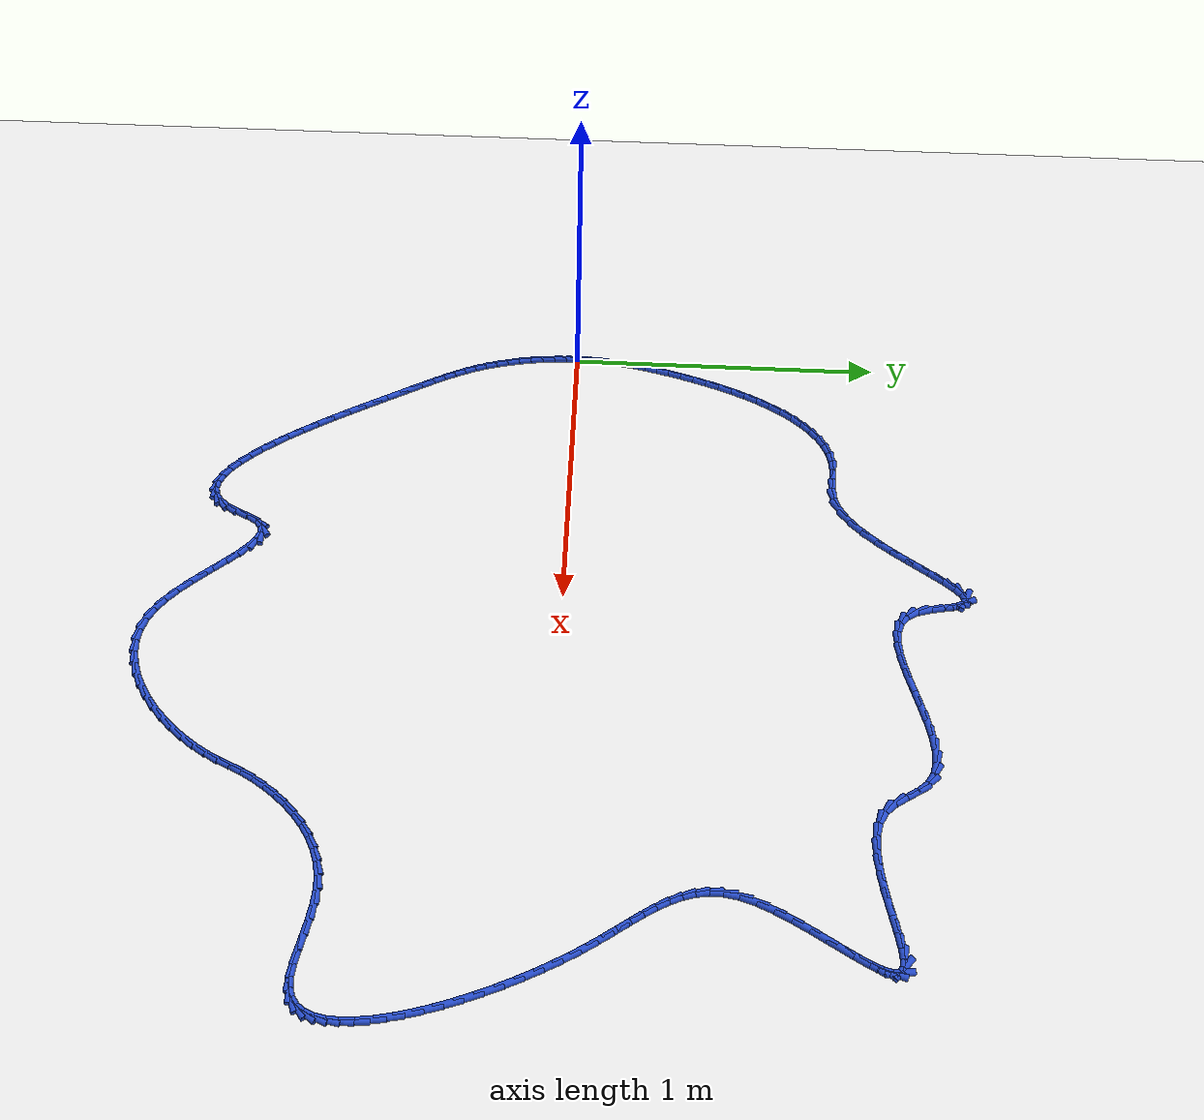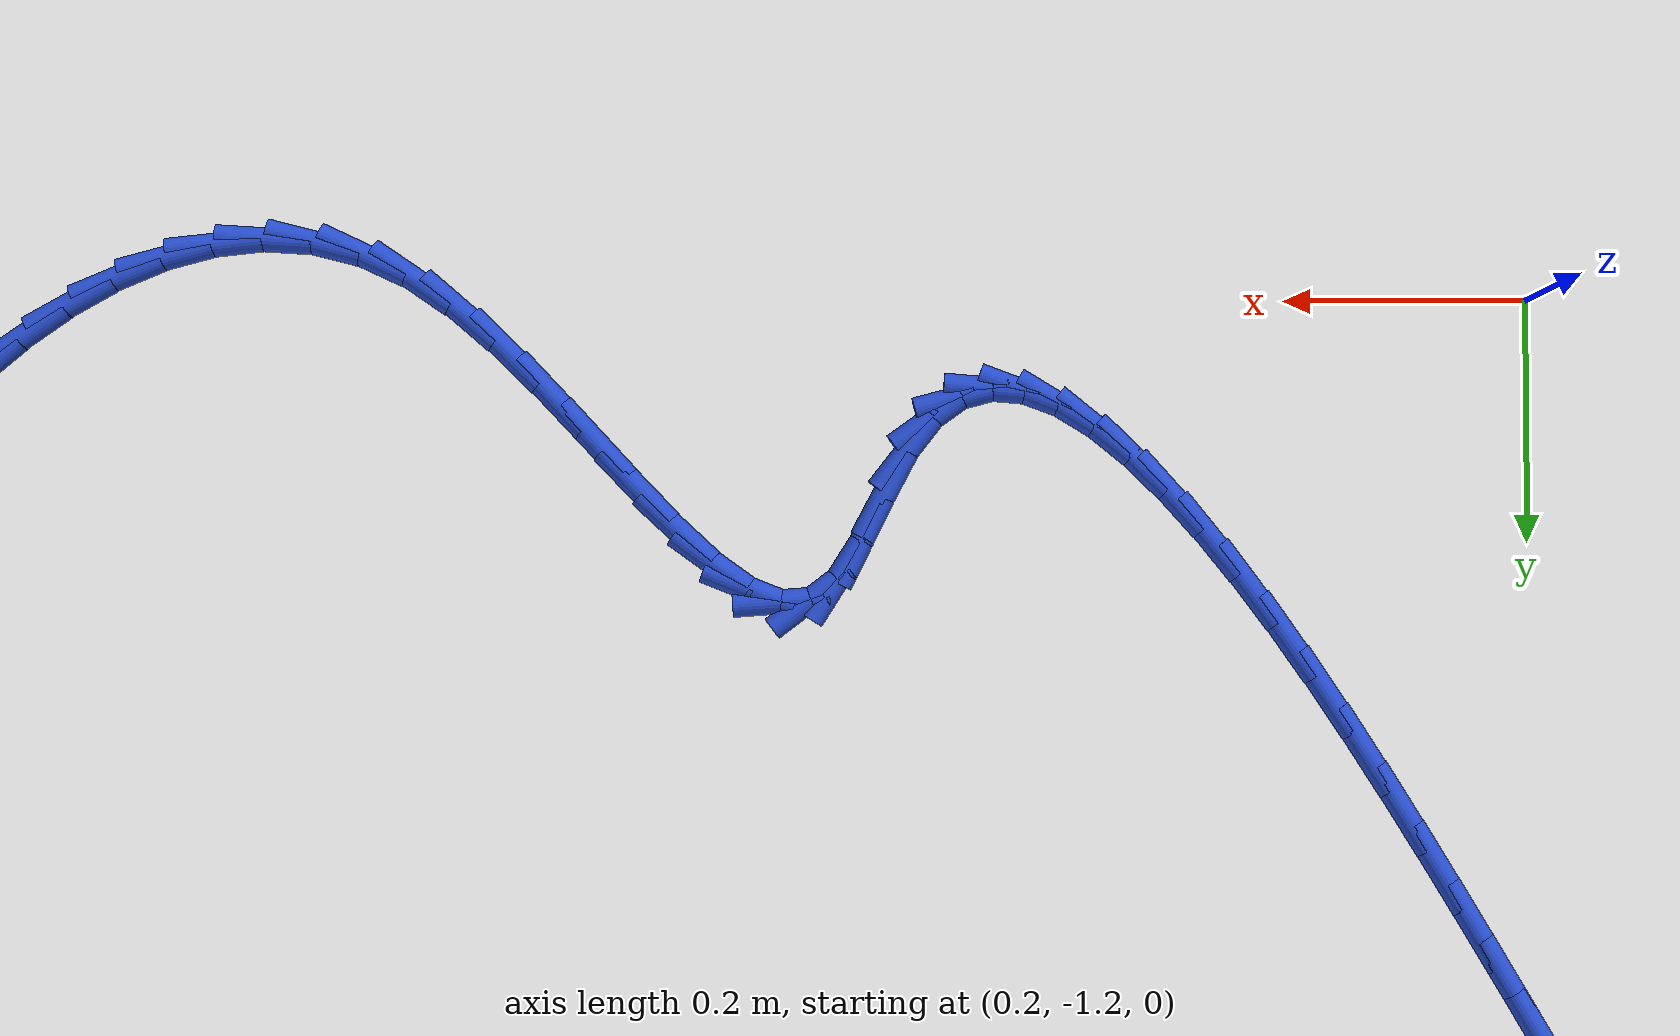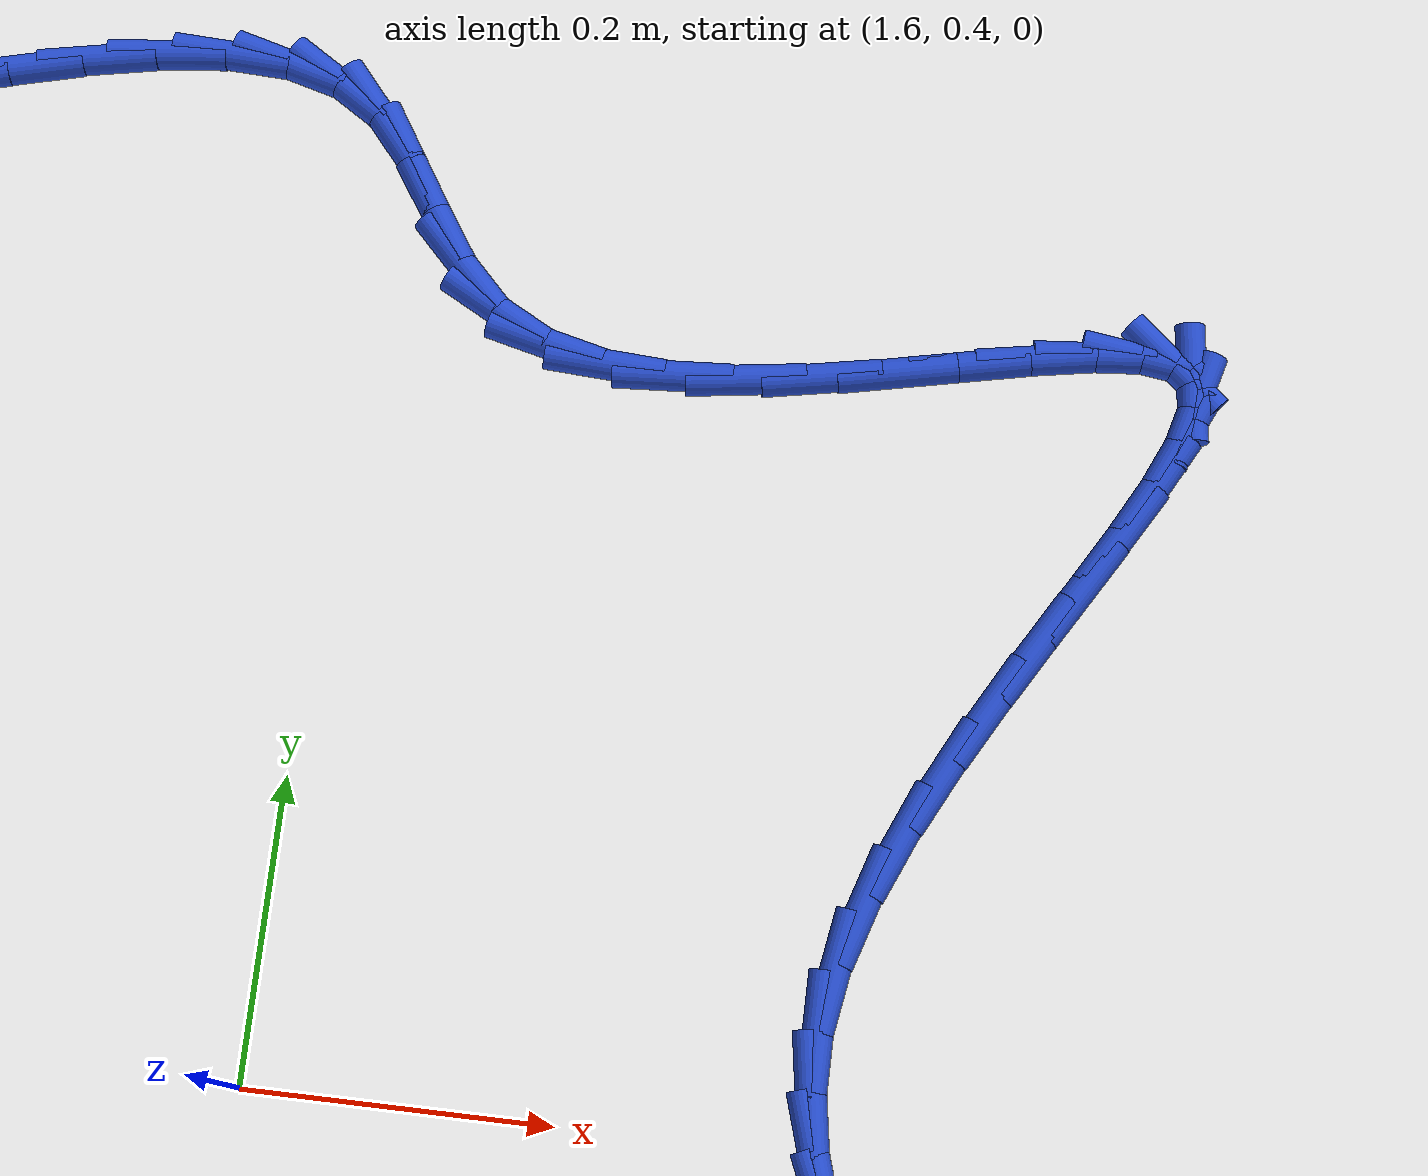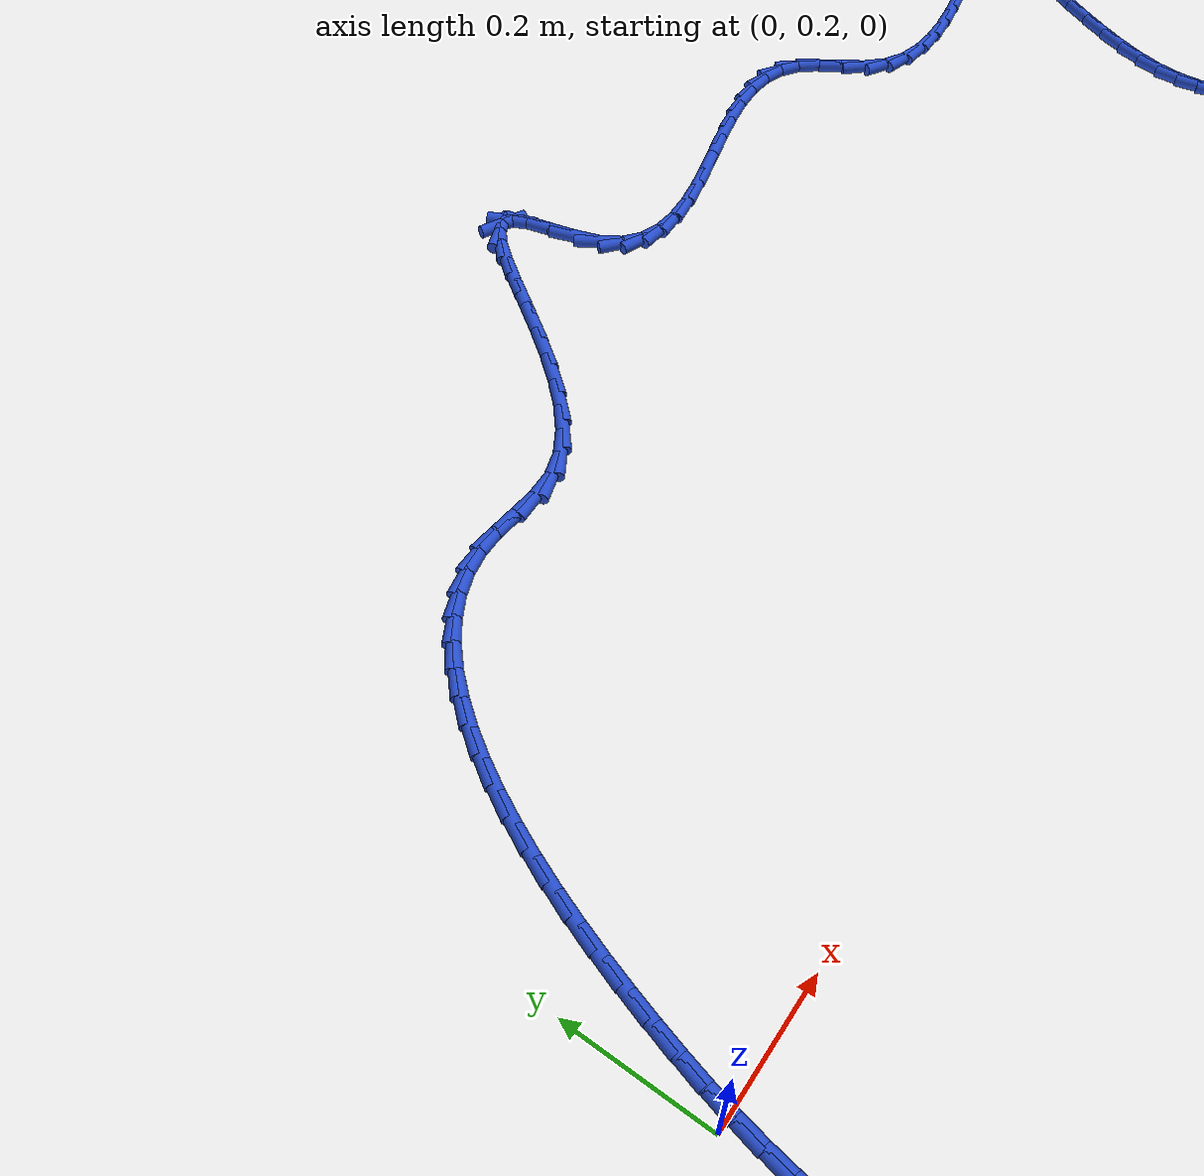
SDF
<sdf version="1.6">
 <world name="default">
  <light name="sun" type="directional">
   <pose>0 0 10 0 -0 0</pose>
   <diffuse>0.8 0.8 0.8 1</diffuse>
   <specular>0.2 0.2 0.2 1</specular>
   <attenuation>
    <range>1000</range>
    <constant>0.9</constant>
    <linear>0.01</linear>
    <quadratic>0.001</quadratic>
   </attenuation>
   <direction>-0.5 0.1 -0.9</direction>
  </light>
  <model name="ground_plane">
   <static>1</static>
   <link name="link">
    <collision name="collision">
     <geometry><plane><normal>0 0 1</normal><size>100 100</size></plane></geometry>
     <surface><friction><ode><mu>100</mu><mu2>50</mu2></ode></friction></surface>
    </collision>
    <visual name="visual">
     <cast_shadows>0</cast_shadows>
     <geometry><plane><normal>0 0 1</normal><size>100 100</size></plane></geometry>
     <material>
      <script><uri>file://media/materials/scripts/gazebo.material</uri><name>Gazebo/WhiteGlow</name></script>
     </material>
    </visual>
   </link>
  </model>
  <gravity>0 0 -9.8</gravity>
  <magnetic_field>6e-06 2.3e-05 -4.2e-05</magnetic_field>
  <atmosphere type="adiabatic"/>
  <physics name="default_physics" default="0" type="ode">
   <max_step_size>0.001</max_step_size>
   <real_time_factor>1</real_time_factor>
   <real_time_update_rate>1000</real_time_update_rate>
  </physics>
  <scene><ambient>0.4 0.4 0.4 1</ambient><background>0.7 0.7 0.7 1</background><shadows>1</shadows></scene>
  <spherical_coordinates>
   <surface_model>EARTH_WGS84</surface_model>
   <latitude_deg>0</latitude_deg>
   <longitude_deg>0</longitude_deg>
   <elevation>0</elevation>
   <heading_deg>0</heading_deg>
  </spherical_coordinates>
  <model name="line">
   <link name="link_0">
    <pose>2.5153490401663703e-17 1.3877787807814457e-17 0.01 0 1.57 1.5471505784857835</pose>
    <collision name="collision">
     <geometry><cylinder><radius>0.01</radius><length>0.08</length></cylinder></geometry>
    </collision>
    <visual name="visual">
     <material>
      <script><name>Gazebo/Blue</name><uri>file://media/materials/scripts/gazebo.material</uri></script>
     </material>
     <geometry><cylinder><radius>0.01</radius><length>0.08</length></cylinder></geometry>
    </visual>
   </link>
   <link name="link_1">
    <pose>0.000923275118051304 0.03903885913328949 0.01 0 1.57 1.5042444246190936</pose>
    <collision name="collision">
     <geometry><cylinder><radius>0.01</radius><length>0.08</length></cylinder></geometry>
    </collision>
    <visual name="visual">
     <material>
      <script><name>Gazebo/Blue</name><uri>file://media/materials/scripts/gazebo.material</uri></script>
     </material>
     <geometry><cylinder><radius>0.01</radius><length>0.08</length></cylinder></geometry>
    </visual>
   </link>
   <link name="link_2">
    <pose>0.0034914588525333636 0.07757105584085955 0.01 0 1.57 1.4627454740002928</pose>
    <collision name="collision">
     <geometry><cylinder><radius>0.01</radius><length>0.08</length></cylinder></geometry>
    </collision>
    <visual name="visual">
     <material>
      <script><name>Gazebo/Blue</name><uri>file://media/materials/scripts/gazebo.material</uri></script>
     </material>
     <geometry><cylinder><radius>0.01</radius><length>0.08</length></cylinder></geometry>
    </visual>
   </link>
   <link name="link_3">
    <pose>0.007645529989852334 0.11586684149822181 0.01 0 1.57 1.4236548072683175</pose>
    <collision name="collision">
     <geometry><cylinder><radius>0.01</radius><length>0.08</length></cylinder></geometry>
    </collision>
    <visual name="visual">
     <material>
      <script><name>Gazebo/Blue</name><uri>file://media/materials/scripts/gazebo.material</uri></script>
     </material>
     <geometry><cylinder><radius>0.01</radius><length>0.08</length></cylinder></geometry>
    </visual>
   </link>
   <link name="link_4">
    <pose>0.013326467316414342 0.15419646748088806 0.01 0 1.57 1.3878259050040362</pose>
    <collision name="collision">
     <geometry><cylinder><radius>0.01</radius><length>0.08</length></cylinder></geometry>
    </collision>
    <visual name="visual">
     <material>
      <script><name>Gazebo/Blue</name><uri>file://media/materials/scripts/gazebo.material</uri></script>
     </material>
     <geometry><cylinder><radius>0.01</radius><length>0.08</length></cylinder></geometry>
    </visual>
   </link>
   <link name="link_5">
    <pose>0.02047524961862552 0.19283018516436995 0.01 0 1.57 1.3559049661492093</pose>
    <collision name="collision">
     <geometry><cylinder><radius>0.01</radius><length>0.08</length></cylinder></geometry>
    </collision>
    <visual name="visual">
     <material>
      <script><name>Gazebo/Blue</name><uri>file://media/materials/scripts/gazebo.material</uri></script>
     </material>
     <geometry><cylinder><radius>0.01</radius><length>0.08</length></cylinder></geometry>
    </visual>
   </link>
   <link name="link_6">
    <pose>0.029032855682891996 0.23203824592417915 0.01 0 1.57 1.3283042895135795</pose>
    <collision name="collision">
     <geometry><cylinder><radius>0.01</radius><length>0.08</length></cylinder></geometry>
    </collision>
    <visual name="visual">
     <material>
      <script><name>Gazebo/Blue</name><uri>file://media/materials/scripts/gazebo.material</uri></script>
     </material>
     <geometry><cylinder><radius>0.01</radius><length>0.08</length></cylinder></geometry>
    </visual>
   </link>
   <link name="link_7">
    <pose>0.038940264295619906 0.27209090113582746 0.01 0 1.57 1.305205933544033</pose>
    <collision name="collision">
     <geometry><cylinder><radius>0.01</radius><length>0.08</length></cylinder></geometry>
    </collision>
    <visual name="visual">
     <material>
      <script><name>Gazebo/Blue</name><uri>file://media/materials/scripts/gazebo.material</uri></script>
     </material>
     <geometry><cylinder><radius>0.01</radius><length>0.08</length></cylinder></geometry>
    </visual>
   </link>
   <link name="link_8">
    <pose>0.05013847081517312 0.3132582760831802 0.01 0 1.57 1.2851180001691027</pose>
    <collision name="collision">
     <geometry><cylinder><radius>0.01</radius><length>0.08</length></cylinder></geometry>
    </collision>
    <visual name="visual">
     <material>
      <script><name>Gazebo/Blue</name><uri>file://media/materials/scripts/gazebo.material</uri></script>
     </material>
     <geometry><cylinder><radius>0.01</radius><length>0.08</length></cylinder></geometry>
    </visual>
   </link>
   <link name="link_9">
    <pose>0.0625895263221571 0.3556502886251262 0.01 0 1.57 1.2634578270486687</pose>
    <collision name="collision">
     <geometry><cylinder><radius>0.01</radius><length>0.08</length></cylinder></geometry>
    </collision>
    <visual name="visual">
     <material>
      <script><name>Gazebo/Blue</name><uri>file://media/materials/scripts/gazebo.material</uri></script>
     </material>
     <geometry><cylinder><radius>0.01</radius><length>0.08</length></cylinder></geometry>
    </visual>
   </link>
   <link name="link_10">
    <pose>0.07631775347409259 0.3989030486517562 0.01 0 1.57 1.2390405952945032</pose>
    <collision name="collision">
     <geometry><cylinder><radius>0.01</radius><length>0.08</length></cylinder></geometry>
    </collision>
    <visual name="visual">
     <material>
      <script><name>Gazebo/Blue</name><uri>file://media/materials/scripts/gazebo.material</uri></script>
     </material>
     <geometry><cylinder><radius>0.01</radius><length>0.08</length></cylinder></geometry>
    </visual>
   </link>
   <link name="link_11">
    <pose>0.09135893180105331 0.4425654937382456 0.01 0 1.57 1.2113824903767378</pose>
    <collision name="collision">
     <geometry><cylinder><radius>0.01</radius><length>0.08</length></cylinder></geometry>
    </collision>
    <visual name="visual">
     <material>
      <script><name>Gazebo/Blue</name><uri>file://media/materials/scripts/gazebo.material</uri></script>
     </material>
     <geometry><cylinder><radius>0.01</radius><length>0.08</length></cylinder></geometry>
    </visual>
   </link>
   <link name="link_12">
    <pose>0.10774884083311295 0.48618656145977013 0.01 0 1.57 1.1798805964561458</pose>
    <collision name="collision">
     <geometry><cylinder><radius>0.01</radius><length>0.08</length></cylinder></geometry>
    </collision>
    <visual name="visual">
     <material>
      <script><name>Gazebo/Blue</name><uri>file://media/materials/scripts/gazebo.material</uri></script>
     </material>
     <geometry><cylinder><radius>0.01</radius><length>0.08</length></cylinder></geometry>
    </visual>
   </link>
   <link name="link_13">
    <pose>0.12552326010034534 0.5293151893915058 0.01 0 1.57 1.1437828212955772</pose>
    <collision name="collision">
     <geometry><cylinder><radius>0.01</radius><length>0.08</length></cylinder></geometry>
    </collision>
    <visual name="visual">
     <material>
      <script><name>Gazebo/Blue</name><uri>file://media/materials/scripts/gazebo.material</uri></script>
     </material>
     <geometry><cylinder><radius>0.01</radius><length>0.08</length></cylinder></geometry>
    </visual>
   </link>
   <link name="link_14">
    <pose>0.14471796913282417 0.5715003151086281 0.01 0 1.57 1.10215036287751</pose>
    <collision name="collision">
     <geometry><cylinder><radius>0.01</radius><length>0.08</length></cylinder></geometry>
    </collision>
    <visual name="visual">
     <material>
      <script><name>Gazebo/Blue</name><uri>file://media/materials/scripts/gazebo.material</uri></script>
     </material>
     <geometry><cylinder><radius>0.01</radius><length>0.08</length></cylinder></geometry>
    </visual>
   </link>
   <link name="link_15">
    <pose>0.16536874746062305 0.6122908761863125 0.01 0 1.57 1.0538134935856716</pose>
    <collision name="collision">
     <geometry><cylinder><radius>0.01</radius><length>0.08</length></cylinder></geometry>
    </collision>
    <visual name="visual">
     <material>
      <script><name>Gazebo/Blue</name><uri>file://media/materials/scripts/gazebo.material</uri></script>
     </material>
     <geometry><cylinder><radius>0.01</radius><length>0.08</length></cylinder></geometry>
    </visual>
   </link>
   <link name="link_16">
    <pose>0.18751137461381603 0.6512358101997353 0.01 0 1.57 0.9973250395359933</pose>
    <collision name="collision">
     <geometry><cylinder><radius>0.01</radius><length>0.08</length></cylinder></geometry>
    </collision>
    <visual name="visual">
     <material>
      <script><name>Gazebo/Blue</name><uri>file://media/materials/scripts/gazebo.material</uri></script>
     </material>
     <geometry><cylinder><radius>0.01</radius><length>0.08</length></cylinder></geometry>
    </visual>
   </link>
   <link name="link_17">
    <pose>0.21118163012247643 0.6878840547240713 0.01 0 1.57 0.9309242295682887</pose>
    <collision name="collision">
     <geometry><cylinder><radius>0.01</radius><length>0.08</length></cylinder></geometry>
    </collision>
    <visual name="visual">
     <material>
      <script><name>Gazebo/Blue</name><uri>file://media/materials/scripts/gazebo.material</uri></script>
     </material>
     <geometry><cylinder><radius>0.01</radius><length>0.08</length></cylinder></geometry>
    </visual>
   </link>
   <link name="link_18">
    <pose>0.23641529351667828 0.721784547334497 0.01 0 1.57 0.8525406614608765</pose>
    <collision name="collision">
     <geometry><cylinder><radius>0.01</radius><length>0.08</length></cylinder></geometry>
    </collision>
    <visual name="visual">
     <material>
      <script><name>Gazebo/Blue</name><uri>file://media/materials/scripts/gazebo.material</uri></script>
     </material>
     <geometry><cylinder><radius>0.01</radius><length>0.08</length></cylinder></geometry>
    </visual>
   </link>
   <link name="link_19">
    <pose>0.26324814432649524 0.7524862256061877 0.01 0 1.57 0.7598989011711493</pose>
    <collision name="collision">
     <geometry><cylinder><radius>0.01</radius><length>0.08</length></cylinder></geometry>
    </collision>
    <visual name="visual">
     <material>
      <script><name>Gazebo/Blue</name><uri>file://media/materials/scripts/gazebo.material</uri></script>
     </material>
     <geometry><cylinder><radius>0.01</radius><length>0.08</length></cylinder></geometry>
    </visual>
   </link>
   <link name="link_20">
    <pose>0.291715962082001 0.7795380271143194 0.01 0 1.57 0.6508278332380614</pose>
    <collision name="collision">
     <geometry><cylinder><radius>0.01</radius><length>0.08</length></cylinder></geometry>
    </collision>
    <visual name="visual">
     <material>
      <script><name>Gazebo/Blue</name><uri>file://media/materials/scripts/gazebo.material</uri></script>
     </material>
     <geometry><cylinder><radius>0.01</radius><length>0.08</length></cylinder></geometry>
    </visual>
   </link>
   <link name="link_21">
    <pose>0.3218545263132693 0.8024888894340675 0.01 0 1.57 0.5239069931924972</pose>
    <collision name="collision">
     <geometry><cylinder><radius>0.01</radius><length>0.08</length></cylinder></geometry>
    </collision>
    <visual name="visual">
     <material>
      <script><name>Gazebo/Blue</name><uri>file://media/materials/scripts/gazebo.material</uri></script>
     </material>
     <geometry><cylinder><radius>0.01</radius><length>0.08</length></cylinder></geometry>
    </visual>
   </link>
   <link name="link_22">
    <pose>0.35369961655037385 0.8208877501406074 0.01 0 1.57 0.37950083316327315</pose>
    <collision name="collision">
     <geometry><cylinder><radius>0.01</radius><length>0.08</length></cylinder></geometry>
    </collision>
    <visual name="visual">
     <material>
      <script><name>Gazebo/Blue</name><uri>file://media/materials/scripts/gazebo.material</uri></script>
     </material>
     <geometry><cylinder><radius>0.01</radius><length>0.08</length></cylinder></geometry>
    </visual>
   </link>
   <link name="link_23">
    <pose>0.38728701232338847 0.8342835468091157 0.01 0 1.57 0.22089554611556805</pose>
    <collision name="collision">
     <geometry><cylinder><radius>0.01</radius><length>0.08</length></cylinder></geometry>
    </collision>
    <visual name="visual">
     <material>
      <script><name>Gazebo/Blue</name><uri>file://media/materials/scripts/gazebo.material</uri></script>
     </material>
     <geometry><cylinder><radius>0.01</radius><length>0.08</length></cylinder></geometry>
    </visual>
   </link>
   <link name="link_24">
    <pose>0.4226524931623869 0.8422252170147673 0.01 0 1.57 0.054821005684071646</pose>
    <collision name="collision">
     <geometry><cylinder><radius>0.01</radius><length>0.08</length></cylinder></geometry>
    </collision>
    <visual name="visual">
     <material>
      <script><name>Gazebo/Blue</name><uri>file://media/materials/scripts/gazebo.material</uri></script>
     </material>
     <geometry><cylinder><radius>0.01</radius><length>0.08</length></cylinder></geometry>
    </visual>
   </link>
   <link name="link_25">
    <pose>0.45983138267797696 0.8442654453996498 0.01 0 1.57 -0.07156752736981528</pose>
    <collision name="collision">
     <geometry><cylinder><radius>0.01</radius><length>0.08</length></cylinder></geometry>
    </collision>
    <visual name="visual">
     <material>
      <script><name>Gazebo/Blue</name><uri>file://media/materials/scripts/gazebo.material</uri></script>
     </material>
     <geometry><cylinder><radius>0.01</radius><length>0.08</length></cylinder></geometry>
    </visual>
   </link>
   <link name="link_26">
    <pose>0.49867358194314676 0.8414808494656638 0.01 0 1.57 -0.06698250012384967</pose>
    <collision name="collision">
     <geometry><cylinder><radius>0.01</radius><length>0.08</length></cylinder></geometry>
    </collision>
    <visual name="visual">
     <material>
      <script><name>Gazebo/Blue</name><uri>file://media/materials/scripts/gazebo.material</uri></script>
     </material>
     <geometry><cylinder><radius>0.01</radius><length>0.08</length></cylinder></geometry>
    </visual>
   </link>
   <link name="link_27">
    <pose>0.538559680865554 0.8388051760340717 0.01 0 1.57 0.07362799343613488</pose>
    <collision name="collision">
     <geometry><cylinder><radius>0.01</radius><length>0.08</length></cylinder></geometry>
    </collision>
    <visual name="visual">
     <material>
      <script><name>Gazebo/Blue</name><uri>file://media/materials/scripts/gazebo.material</uri></script>
     </material>
     <geometry><cylinder><radius>0.01</radius><length>0.08</length></cylinder></geometry>
    </visual>
   </link>
   <link name="link_28">
    <pose>0.5787971467343916 0.8417731450467943 0.01 0 1.57 0.3278715144154664</pose>
    <collision name="collision">
     <geometry><cylinder><radius>0.01</radius><length>0.08</length></cylinder></geometry>
    </collision>
    <visual name="visual">
     <material>
      <script><name>Gazebo/Blue</name><uri>file://media/materials/scripts/gazebo.material</uri></script>
     </material>
     <geometry><cylinder><radius>0.01</radius><length>0.08</length></cylinder></geometry>
    </visual>
   </link>
   <link name="link_29">
    <pose>0.6187249516236565 0.8553545235972684 0.01 0 1.57 0.5558149710328105</pose>
    <collision name="collision">
     <geometry><cylinder><radius>0.01</radius><length>0.08</length></cylinder></geometry>
    </collision>
    <visual name="visual">
     <material>
      <script><name>Gazebo/Blue</name><uri>file://media/materials/scripts/gazebo.material</uri></script>
     </material>
     <geometry><cylinder><radius>0.01</radius><length>0.08</length></cylinder></geometry>
    </visual>
   </link>
   <link name="link_30">
    <pose>0.6579497776390179 0.8797184256114372 0.01 0 1.57 0.7100531514031744</pose>
    <collision name="collision">
     <geometry><cylinder><radius>0.01</radius><length>0.08</length></cylinder></geometry>
    </collision>
    <visual name="visual">
     <material>
      <script><name>Gazebo/Blue</name><uri>file://media/materials/scripts/gazebo.material</uri></script>
     </material>
     <geometry><cylinder><radius>0.01</radius><length>0.08</length></cylinder></geometry>
    </visual>
   </link>
   <link name="link_31">
    <pose>0.6962134422620886 0.9126106786463484 0.01 0 1.57 0.8129848368860437</pose>
    <collision name="collision">
     <geometry><cylinder><radius>0.01</radius><length>0.08</length></cylinder></geometry>
    </collision>
    <visual name="visual">
     <material>
      <script><name>Gazebo/Blue</name><uri>file://media/materials/scripts/gazebo.material</uri></script>
     </material>
     <geometry><cylinder><radius>0.01</radius><length>0.08</length></cylinder></geometry>
    </visual>
   </link>
   <link name="link_32">
    <pose>0.7332588014908799 0.9517584872847562 0.01 0 1.57 0.8811730232288056</pose>
    <collision name="collision">
     <geometry><cylinder><radius>0.01</radius><length>0.08</length></cylinder></geometry>
    </collision>
    <visual name="visual">
     <material>
      <script><name>Gazebo/Blue</name><uri>file://media/materials/scripts/gazebo.material</uri></script>
     </material>
     <geometry><cylinder><radius>0.01</radius><length>0.08</length></cylinder></geometry>
    </visual>
   </link>
   <link name="link_33">
    <pose>0.7688287113234029 0.9948890561094166 0.01 0 1.57 0.9243484792010429</pose>
    <collision name="collision">
     <geometry><cylinder><radius>0.01</radius><length>0.08</length></cylinder></geometry>
    </collision>
    <visual name="visual">
     <material>
      <script><name>Gazebo/Blue</name><uri>file://media/materials/scripts/gazebo.material</uri></script>
     </material>
     <geometry><cylinder><radius>0.01</radius><length>0.08</length></cylinder></geometry>
    </visual>
   </link>
   <link name="link_34">
    <pose>0.802666027757669 1.0397295897030845 0.01 0 1.57 0.9472548698115287</pose>
    <collision name="collision">
     <geometry><cylinder><radius>0.01</radius><length>0.08</length></cylinder></geometry>
    </collision>
    <visual name="visual">
     <material>
      <script><name>Gazebo/Blue</name><uri>file://media/materials/scripts/gazebo.material</uri></script>
     </material>
     <geometry><cylinder><radius>0.01</radius><length>0.08</length></cylinder></geometry>
    </visual>
   </link>
   <link name="link_35">
    <pose>0.8345136067916895 1.0840072926485156 0.01 0 1.57 0.9505593973106484</pose>
    <collision name="collision">
     <geometry><cylinder><radius>0.01</radius><length>0.08</length></cylinder></geometry>
    </collision>
    <visual name="visual">
     <material>
      <script><name>Gazebo/Blue</name><uri>file://media/materials/scripts/gazebo.material</uri></script>
     </material>
     <geometry><cylinder><radius>0.01</radius><length>0.08</length></cylinder></geometry>
    </visual>
   </link>
   <link name="link_36">
    <pose>0.8641143044234756 1.1254493695284646 0.01 0 1.57 0.9300057607816296</pose>
    <collision name="collision">
     <geometry><cylinder><radius>0.01</radius><length>0.08</length></cylinder></geometry>
    </collision>
    <visual name="visual">
     <material>
      <script><name>Gazebo/Blue</name><uri>file://media/materials/scripts/gazebo.material</uri></script>
     </material>
     <geometry><cylinder><radius>0.01</radius><length>0.08</length></cylinder></geometry>
    </visual>
   </link>
   <link name="link_37">
    <pose>0.8912109766510389 1.1617830249256875 0.01 0 1.57 0.871823621935451</pose>
    <collision name="collision">
     <geometry><cylinder><radius>0.01</radius><length>0.08</length></cylinder></geometry>
    </collision>
    <visual name="visual">
     <material>
      <script><name>Gazebo/Blue</name><uri>file://media/materials/scripts/gazebo.material</uri></script>
     </material>
     <geometry><cylinder><radius>0.01</radius><length>0.08</length></cylinder></geometry>
    </visual>
   </link>
   <link name="link_38">
    <pose>0.9155464794723907 1.1907354634229397 0.01 0 1.57 0.7357349190350344</pose>
    <collision name="collision">
     <geometry><cylinder><radius>0.01</radius><length>0.08</length></cylinder></geometry>
    </collision>
    <visual name="visual">
     <material>
      <script><name>Gazebo/Blue</name><uri>file://media/materials/scripts/gazebo.material</uri></script>
     </material>
     <geometry><cylinder><radius>0.01</radius><length>0.08</length></cylinder></geometry>
    </visual>
   </link>
   <link name="link_39">
    <pose>0.9368636688855416 1.2100338896029763 0.01 0 1.57 0.38788703605239805</pose>
    <collision name="collision">
     <geometry><cylinder><radius>0.01</radius><length>0.08</length></cylinder></geometry>
    </collision>
    <visual name="visual">
     <material>
      <script><name>Gazebo/Blue</name><uri>file://media/materials/scripts/gazebo.material</uri></script>
     </material>
     <geometry><cylinder><radius>0.01</radius><length>0.08</length></cylinder></geometry>
    </visual>
   </link>
   <link name="link_40">
    <pose>0.9549054008885036 1.2174055080485522 0.01 0 1.57 -0.4398515289322776</pose>
    <collision name="collision">
     <geometry><cylinder><radius>0.01</radius><length>0.08</length></cylinder></geometry>
    </collision>
    <visual name="visual">
     <material>
      <script><name>Gazebo/Blue</name><uri>file://media/materials/scripts/gazebo.material</uri></script>
     </material>
     <geometry><cylinder><radius>0.01</radius><length>0.08</length></cylinder></geometry>
    </visual>
   </link>
   <link name="link_41">
    <pose>0.9694145314792878 1.2105775233424232 0.01 0 1.57 -1.1345703052887388</pose>
    <collision name="collision">
     <geometry><cylinder><radius>0.01</radius><length>0.08</length></cylinder></geometry>
    </collision>
    <visual name="visual">
     <material>
      <script><name>Gazebo/Blue</name><uri>file://media/materials/scripts/gazebo.material</uri></script>
     </material>
     <geometry><cylinder><radius>0.01</radius><length>0.08</length></cylinder></geometry>
    </visual>
   </link>
   <link name="link_42">
    <pose>0.9801926773302033 1.1874572992600771 0.01 0 1.57 -1.3466487477814062</pose>
    <collision name="collision">
     <geometry><cylinder><radius>0.01</radius><length>0.08</length></cylinder></geometry>
    </collision>
    <visual name="visual">
     <material>
      <script><name>Gazebo/Blue</name><uri>file://media/materials/scripts/gazebo.material</uri></script>
     </material>
     <geometry><cylinder><radius>0.01</radius><length>0.08</length></cylinder></geometry>
    </visual>
   </link>
   <link name="link_43">
    <pose>0.988579727774339 1.1506685164688686 0.01 0 1.57 -1.3637411586916737</pose>
    <collision name="collision">
     <geometry><cylinder><radius>0.01</radius><length>0.08</length></cylinder></geometry>
    </collision>
    <visual name="visual">
     <material>
      <script><name>Gazebo/Blue</name><uri>file://media/materials/scripts/gazebo.material</uri></script>
     </material>
     <geometry><cylinder><radius>0.01</radius><length>0.08</length></cylinder></geometry>
    </visual>
   </link>
   <link name="link_44">
    <pose>0.9975653738728121 1.1078931186843897 0.01 0 1.57 -1.2702511035892534</pose>
    <collision name="collision">
     <geometry><cylinder><radius>0.01</radius><length>0.08</length></cylinder></geometry>
    </collision>
    <visual name="visual">
     <material>
      <script><name>Gazebo/Blue</name><uri>file://media/materials/scripts/gazebo.material</uri></script>
     </material>
     <geometry><cylinder><radius>0.01</radius><length>0.08</length></cylinder></geometry>
    </visual>
   </link>
   <link name="link_45">
    <pose>1.0102204074381134 1.0670617030979097 0.01 0 1.57 -1.023911564125688</pose>
    <collision name="collision">
     <geometry><cylinder><radius>0.01</radius><length>0.08</length></cylinder></geometry>
    </collision>
    <visual name="visual">
     <material>
      <script><name>Gazebo/Blue</name><uri>file://media/materials/scripts/gazebo.material</uri></script>
     </material>
     <geometry><cylinder><radius>0.01</radius><length>0.08</length></cylinder></geometry>
    </visual>
   </link>
   <link name="link_46">
    <pose>1.0293908697085046 1.0355741730770303 0.01 0 1.57 -0.660660819883588</pose>
    <collision name="collision">
     <geometry><cylinder><radius>0.01</radius><length>0.08</length></cylinder></geometry>
    </collision>
    <visual name="visual">
     <material>
      <script><name>Gazebo/Blue</name><uri>file://media/materials/scripts/gazebo.material</uri></script>
     </material>
     <geometry><cylinder><radius>0.01</radius><length>0.08</length></cylinder></geometry>
    </visual>
   </link>
   <link name="link_47">
    <pose>1.0555552871307003 1.0152401215679852 0.01 0 1.57 -0.32121999910336907</pose>
    <collision name="collision">
     <geometry><cylinder><radius>0.01</radius><length>0.08</length></cylinder></geometry>
    </collision>
    <visual name="visual">
     <material>
      <script><name>Gazebo/Blue</name><uri>file://media/materials/scripts/gazebo.material</uri></script>
     </material>
     <geometry><cylinder><radius>0.01</radius><length>0.08</length></cylinder></geometry>
    </visual>
   </link>
   <link name="link_48">
    <pose>1.0877736661340152 1.004519651467569 0.01 0 1.57 -0.07202446698710534</pose>
    <collision name="collision">
     <geometry><cylinder><radius>0.01</radius><length>0.08</length></cylinder></geometry>
    </collision>
    <visual name="visual">
     <material>
      <script><name>Gazebo/Blue</name><uri>file://media/materials/scripts/gazebo.material</uri></script>
     </material>
     <geometry><cylinder><radius>0.01</radius><length>0.08</length></cylinder></geometry>
    </visual>
   </link>
   <link name="link_49">
    <pose>1.1250868154698648 1.0018275350249255 0.01 0 1.57 0.0902517305781408</pose>
    <collision name="collision">
     <geometry><cylinder><radius>0.01</radius><length>0.08</length></cylinder></geometry>
    </collision>
    <visual name="visual">
     <material>
      <script><name>Gazebo/Blue</name><uri>file://media/materials/scripts/gazebo.material</uri></script>
     </material>
     <geometry><cylinder><radius>0.01</radius><length>0.08</length></cylinder></geometry>
    </visual>
   </link>
   <link name="link_50">
    <pose>1.1665355438896647 1.0055785444891976 0.01 0 1.57 0.19057502289999953</pose>
    <collision name="collision">
     <geometry><cylinder><radius>0.01</radius><length>0.08</length></cylinder></geometry>
    </collision>
    <visual name="visual">
     <material>
      <script><name>Gazebo/Blue</name><uri>file://media/materials/scripts/gazebo.material</uri></script>
     </material>
     <geometry><cylinder><radius>0.01</radius><length>0.08</length></cylinder></geometry>
    </visual>
   </link>
   <link name="link_51">
    <pose>1.2111606601448308 1.0141874521095293 0.01 0 1.57 0.2484115049144183</pose>
    <collision name="collision">
     <geometry><cylinder><radius>0.01</radius><length>0.08</length></cylinder></geometry>
    </collision>
    <visual name="visual">
     <material>
      <script><name>Gazebo/Blue</name><uri>file://media/materials/scripts/gazebo.material</uri></script>
     </material>
     <geometry><cylinder><radius>0.01</radius><length>0.08</length></cylinder></geometry>
    </visual>
   </link>
   <link name="link_52">
    <pose>1.258002972986778 1.0260690301350635 0.01 0 1.57 0.27495344594959714</pose>
    <collision name="collision">
     <geometry><cylinder><radius>0.01</radius><length>0.08</length></cylinder></geometry>
    </collision>
    <visual name="visual">
     <material>
      <script><name>Gazebo/Blue</name><uri>file://media/materials/scripts/gazebo.material</uri></script>
     </material>
     <geometry><cylinder><radius>0.01</radius><length>0.08</length></cylinder></geometry>
    </visual>
   </link>
   <link name="link_53">
    <pose>1.3061032911669226 1.0396380508149439 0.01 0 1.57 0.27529637345718416</pose>
    <collision name="collision">
     <geometry><cylinder><radius>0.01</radius><length>0.08</length></cylinder></geometry>
    </collision>
    <visual name="visual">
     <material>
      <script><name>Gazebo/Blue</name><uri>file://media/materials/scripts/gazebo.material</uri></script>
     </material>
     <geometry><cylinder><radius>0.01</radius><length>0.08</length></cylinder></geometry>
    </visual>
   </link>
   <link name="link_54">
    <pose>1.3545024234366798 1.053309286398314 0.01 0 1.57 0.249970842008268</pose>
    <collision name="collision">
     <geometry><cylinder><radius>0.01</radius><length>0.08</length></cylinder></geometry>
    </collision>
    <visual name="visual">
     <material>
      <script><name>Gazebo/Blue</name><uri>file://media/materials/scripts/gazebo.material</uri></script>
     </material>
     <geometry><cylinder><radius>0.01</radius><length>0.08</length></cylinder></geometry>
    </visual>
   </link>
   <link name="link_55">
    <pose>1.4022411785474655 1.065497509134317 0.01 0 1.57 0.19522934906371991</pose>
    <collision name="collision">
     <geometry><cylinder><radius>0.01</radius><length>0.08</length></cylinder></geometry>
    </collision>
    <visual name="visual">
     <material>
      <script><name>Gazebo/Blue</name><uri>file://media/materials/scripts/gazebo.material</uri></script>
     </material>
     <geometry><cylinder><radius>0.01</radius><length>0.08</length></cylinder></geometry>
    </visual>
   </link>
   <link name="link_56">
    <pose>1.4483603652506947 1.0746174912720963 0.01 0 1.57 0.10222555881255425</pose>
    <collision name="collision">
     <geometry><cylinder><radius>0.01</radius><length>0.08</length></cylinder></geometry>
    </collision>
    <visual name="visual">
     <material>
      <script><name>Gazebo/Blue</name><uri>file://media/materials/scripts/gazebo.material</uri></script>
     </material>
     <geometry><cylinder><radius>0.01</radius><length>0.08</length></cylinder></geometry>
    </visual>
   </link>
   <link name="link_57">
    <pose>1.4919007922977832 1.0790840050607955 0.01 0 1.57 -0.04427286642482377</pose>
    <collision name="collision">
     <geometry><cylinder><radius>0.01</radius><length>0.08</length></cylinder></geometry>
    </collision>
    <visual name="visual">
     <material>
      <script><name>Gazebo/Blue</name><uri>file://media/materials/scripts/gazebo.material</uri></script>
     </material>
     <geometry><cylinder><radius>0.01</radius><length>0.08</length></cylinder></geometry>
    </visual>
   </link>
   <link name="link_58">
    <pose>1.5319032684401468 1.077311822749558 0.01 0 1.57 -0.26396555960565266</pose>
    <collision name="collision">
     <geometry><cylinder><radius>0.01</radius><length>0.08</length></cylinder></geometry>
    </collision>
    <visual name="visual">
     <material>
      <script><name>Gazebo/Blue</name><uri>file://media/materials/scripts/gazebo.material</uri></script>
     </material>
     <geometry><cylinder><radius>0.01</radius><length>0.08</length></cylinder></geometry>
    </visual>
   </link>
   <link name="link_59">
    <pose>1.567408602429201 1.0677157165875273 0.01 0 1.57 -0.5639569300416017</pose>
    <collision name="collision">
     <geometry><cylinder><radius>0.01</radius><length>0.08</length></cylinder></geometry>
    </collision>
    <visual name="visual">
     <material>
      <script><name>Gazebo/Blue</name><uri>file://media/materials/scripts/gazebo.material</uri></script>
     </material>
     <geometry><cylinder><radius>0.01</radius><length>0.08</length></cylinder></geometry>
    </visual>
   </link>
   <link name="link_60">
    <pose>1.5974576030163616 1.048710458823846 0.01 0 1.57 -0.8688384375488674</pose>
    <collision name="collision">
     <geometry><cylinder><radius>0.01</radius><length>0.08</length></cylinder></geometry>
    </collision>
    <visual name="visual">
     <material>
      <script><name>Gazebo/Blue</name><uri>file://media/materials/scripts/gazebo.material</uri></script>
     </material>
     <geometry><cylinder><radius>0.01</radius><length>0.08</length></cylinder></geometry>
    </visual>
   </link>
   <link name="link_61">
    <pose>1.621846457739842 1.0198697808917465 0.01 0 1.57 -1.0075575633804947</pose>
    <collision name="collision">
     <geometry><cylinder><radius>0.01</radius><length>0.08</length></cylinder></geometry>
    </collision>
    <visual name="visual">
     <material>
      <script><name>Gazebo/Blue</name><uri>file://media/materials/scripts/gazebo.material</uri></script>
     </material>
     <geometry><cylinder><radius>0.01</radius><length>0.08</length></cylinder></geometry>
    </visual>
   </link>
   <link name="link_62">
    <pose>1.6435036886910224 0.9855732784630096 0.01 0 1.57 -0.9845311564287268</pose>
    <collision name="collision">
     <geometry><cylinder><radius>0.01</radius><length>0.08</length></cylinder></geometry>
    </collision>
    <visual name="visual">
     <material>
      <script><name>Gazebo/Blue</name><uri>file://media/materials/scripts/gazebo.material</uri></script>
     </material>
     <geometry><cylinder><radius>0.01</radius><length>0.08</length></cylinder></geometry>
    </visual>
   </link>
   <link name="link_63">
    <pose>1.666169615058855 0.951446067626839 0.01 0 1.57 -0.8019436208430275</pose>
    <collision name="collision">
     <geometry><cylinder><radius>0.01</radius><length>0.08</length></cylinder></geometry>
    </collision>
    <visual name="visual">
     <material>
      <script><name>Gazebo/Blue</name><uri>file://media/materials/scripts/gazebo.material</uri></script>
     </material>
     <geometry><cylinder><radius>0.01</radius><length>0.08</length></cylinder></geometry>
    </visual>
   </link>
   <link name="link_64">
    <pose>1.6935825939955085 0.9231106213152334 0.01 0 1.57 -0.49427795770208377</pose>
    <collision name="collision">
     <geometry><cylinder><radius>0.01</radius><length>0.08</length></cylinder></geometry>
    </collision>
    <visual name="visual">
     <material>
      <script><name>Gazebo/Blue</name><uri>file://media/materials/scripts/gazebo.material</uri></script>
     </material>
     <geometry><cylinder><radius>0.01</radius><length>0.08</length></cylinder></geometry>
    </visual>
   </link>
   <link name="link_65">
    <pose>1.7281956923925312 0.9044577680749949 0.01 0 1.57 -0.23584991319914753</pose>
    <collision name="collision">
     <geometry><cylinder><radius>0.01</radius><length>0.08</length></cylinder></geometry>
    </collision>
    <visual name="visual">
     <material>
      <script><name>Gazebo/Blue</name><uri>file://media/materials/scripts/gazebo.material</uri></script>
     </material>
     <geometry><cylinder><radius>0.01</radius><length>0.08</length></cylinder></geometry>
    </visual>
   </link>
   <link name="link_66">
    <pose>1.7689606237220714 0.8946610370420068 0.01 0 1.57 -0.05654275098243486</pose>
    <collision name="collision">
     <geometry><cylinder><radius>0.01</radius><length>0.08</length></cylinder></geometry>
    </collision>
    <visual name="visual">
     <material>
      <script><name>Gazebo/Blue</name><uri>file://media/materials/scripts/gazebo.material</uri></script>
     </material>
     <geometry><cylinder><radius>0.01</radius><length>0.08</length></cylinder></geometry>
    </visual>
   </link>
   <link name="link_67">
    <pose>1.8142384409083525 0.8920981728879662 0.01 0 1.57 0.06323098976073235</pose>
    <collision name="collision">
     <geometry><cylinder><radius>0.01</radius><length>0.08</length></cylinder></geometry>
    </collision>
    <visual name="visual">
     <material>
      <script><name>Gazebo/Blue</name><uri>file://media/materials/scripts/gazebo.material</uri></script>
     </material>
     <geometry><cylinder><radius>0.01</radius><length>0.08</length></cylinder></geometry>
    </visual>
   </link>
   <link name="link_68">
    <pose>1.8623901968755974 0.895146920284571 0.01 0 1.57 0.1415568025229246</pose>
    <collision name="collision">
     <geometry><cylinder><radius>0.01</radius><length>0.08</length></cylinder></geometry>
    </collision>
    <visual name="visual">
     <material>
      <script><name>Gazebo/Blue</name><uri>file://media/materials/scripts/gazebo.material</uri></script>
     </material>
     <geometry><cylinder><radius>0.01</radius><length>0.08</length></cylinder></geometry>
    </visual>
   </link>
   <link name="link_69">
    <pose>1.9117769445480282 0.9021850239035176 0.01 0 1.57 0.18970156196786686</pose>
    <collision name="collision">
     <geometry><cylinder><radius>0.01</radius><length>0.08</length></cylinder></geometry>
    </collision>
    <visual name="visual">
     <material>
      <script><name>Gazebo/Blue</name><uri>file://media/materials/scripts/gazebo.material</uri></script>
     </material>
     <geometry><cylinder><radius>0.01</radius><length>0.08</length></cylinder></geometry>
    </visual>
   </link>
   <link name="link_70">
    <pose>1.9607597368498693 0.9115902284165041 0.01 0 1.57 0.2129563553523567</pose>
    <collision name="collision">
     <geometry><cylinder><radius>0.01</radius><length>0.08</length></cylinder></geometry>
    </collision>
    <visual name="visual">
     <material>
      <script><name>Gazebo/Blue</name><uri>file://media/materials/scripts/gazebo.material</uri></script>
     </material>
     <geometry><cylinder><radius>0.01</radius><length>0.08</length></cylinder></geometry>
    </visual>
   </link>
   <link name="link_71">
    <pose>2.0076996267053415 0.9217402784952268 0.01 0 1.57 0.2111609703622986</pose>
    <collision name="collision">
     <geometry><cylinder><radius>0.01</radius><length>0.08</length></cylinder></geometry>
    </collision>
    <visual name="visual">
     <material>
      <script><name>Gazebo/Blue</name><uri>file://media/materials/scripts/gazebo.material</uri></script>
     </material>
     <geometry><cylinder><radius>0.01</radius><length>0.08</length></cylinder></geometry>
    </visual>
   </link>
   <link name="link_72">
    <pose>2.050957667038669 0.9310129188113839 0.01 0 1.57 0.17666970629588838</pose>
    <collision name="collision">
     <geometry><cylinder><radius>0.01</radius><length>0.08</length></cylinder></geometry>
    </collision>
    <visual name="visual">
     <material>
      <script><name>Gazebo/Blue</name><uri>file://media/materials/scripts/gazebo.material</uri></script>
     </material>
     <geometry><cylinder><radius>0.01</radius><length>0.08</length></cylinder></geometry>
    </visual>
   </link>
   <link name="link_73">
    <pose>2.0888949107740755 0.9377858940366727 0.01 0 1.57 0.08537199707806459</pose>
    <collision name="collision">
     <geometry><cylinder><radius>0.01</radius><length>0.08</length></cylinder></geometry>
    </collision>
    <visual name="visual">
     <material>
      <script><name>Gazebo/Blue</name><uri>file://media/materials/scripts/gazebo.material</uri></script>
     </material>
     <geometry><cylinder><radius>0.01</radius><length>0.08</length></cylinder></geometry>
    </visual>
   </link>
   <link name="link_74">
    <pose>2.119872410835783 0.9404369488427903 0.01 0 1.57 -0.13734631011938914</pose>
    <collision name="collision">
     <geometry><cylinder><radius>0.01</radius><length>0.08</length></cylinder></geometry>
    </collision>
    <visual name="visual">
     <material>
      <script><name>Gazebo/Blue</name><uri>file://media/materials/scripts/gazebo.material</uri></script>
     </material>
     <geometry><cylinder><radius>0.01</radius><length>0.08</length></cylinder></geometry>
    </visual>
   </link>
   <link name="link_75">
    <pose>2.142251220148015 0.9373438279014338 0.01 0 1.57 -0.7052189739964236</pose>
    <collision name="collision">
     <geometry><cylinder><radius>0.01</radius><length>0.08</length></cylinder></geometry>
    </collision>
    <visual name="visual">
     <material>
      <script><name>Gazebo/Blue</name><uri>file://media/materials/scripts/gazebo.material</uri></script>
     </material>
     <geometry><cylinder><radius>0.01</radius><length>0.08</length></cylinder></geometry>
    </visual>
   </link>
   <link name="link_76">
    <pose>2.154467777724711 0.9269444902627202 0.01 0 1.57 -1.4561961126628769</pose>
    <collision name="collision">
     <geometry><cylinder><radius>0.01</radius><length>0.08</length></cylinder></geometry>
    </collision>
    <visual name="visual">
     <material>
      <script><name>Gazebo/Blue</name><uri>file://media/materials/scripts/gazebo.material</uri></script>
     </material>
     <geometry><cylinder><radius>0.01</radius><length>0.08</length></cylinder></geometry>
    </visual>
   </link>
   <link name="link_77">
    <pose>2.1565401516976164 0.9089402157641203 0.01 0 1.57 1.3115790739967352</pose>
    <collision name="collision">
     <geometry><cylinder><radius>0.01</radius><length>0.08</length></cylinder></geometry>
    </collision>
    <visual name="visual">
     <material>
      <script><name>Gazebo/Blue</name><uri>file://media/materials/scripts/gazebo.material</uri></script>
     </material>
     <geometry><cylinder><radius>0.01</radius><length>0.08</length></cylinder></geometry>
    </visual>
   </link>
   <link name="link_78">
    <pose>2.149987812498421 0.8842315241371852 0.01 0 1.57 1.150978818763394</pose>
    <collision name="collision">
     <geometry><cylinder><radius>0.01</radius><length>0.08</length></cylinder></geometry>
    </collision>
    <visual name="visual">
     <material>
      <script><name>Gazebo/Blue</name><uri>file://media/materials/scripts/gazebo.material</uri></script>
     </material>
     <geometry><cylinder><radius>0.01</radius><length>0.08</length></cylinder></geometry>
    </visual>
   </link>
   <link name="link_79">
    <pose>2.1363895576536014 0.8537663224252269 0.01 0 1.57 1.0752786275189683</pose>
    <collision name="collision">
     <geometry><cylinder><radius>0.01</radius><length>0.08</length></cylinder></geometry>
    </collision>
    <visual name="visual">
     <material>
      <script><name>Gazebo/Blue</name><uri>file://media/materials/scripts/gazebo.material</uri></script>
     </material>
     <geometry><cylinder><radius>0.01</radius><length>0.08</length></cylinder></geometry>
    </visual>
   </link>
   <link name="link_80">
    <pose>2.1173241846896342 0.8184925176715573 0.01 0 1.57 1.0403375554508574</pose>
    <collision name="collision">
     <geometry><cylinder><radius>0.01</radius><length>0.08</length></cylinder></geometry>
    </collision>
    <visual name="visual">
     <material>
      <script><name>Gazebo/Blue</name><uri>file://media/materials/scripts/gazebo.material</uri></script>
     </material>
     <geometry><cylinder><radius>0.01</radius><length>0.08</length></cylinder></geometry>
    </visual>
   </link>
   <link name="link_81">
    <pose>2.094370491132997 0.7793580169194887 0.01 0 1.57 1.0297677423459055</pose>
    <collision name="collision">
     <geometry><cylinder><radius>0.01</radius><length>0.08</length></cylinder></geometry>
    </collision>
    <visual name="visual">
     <material>
      <script><name>Gazebo/Blue</name><uri>file://media/materials/scripts/gazebo.material</uri></script>
     </material>
     <geometry><cylinder><radius>0.01</radius><length>0.08</length></cylinder></geometry>
    </visual>
   </link>
   <link name="link_82">
    <pose>2.069107274510165 0.7373107272123332 0.01 0 1.57 1.0373113061208428</pose>
    <collision name="collision">
     <geometry><cylinder><radius>0.01</radius><length>0.08</length></cylinder></geometry>
    </collision>
    <visual name="visual">
     <material>
      <script><name>Gazebo/Blue</name><uri>file://media/materials/scripts/gazebo.material</uri></script>
     </material>
     <geometry><cylinder><radius>0.01</radius><length>0.08</length></cylinder></geometry>
    </visual>
   </link>
   <link name="link_83">
    <pose>2.0431133323476156 0.6932985555934026 0.01 0 1.57 1.0614998646317197</pose>
    <collision name="collision">
     <geometry><cylinder><radius>0.01</radius><length>0.08</length></cylinder></geometry>
    </collision>
    <visual name="visual">
     <material>
      <script><name>Gazebo/Blue</name><uri>file://media/materials/scripts/gazebo.material</uri></script>
     </material>
     <geometry><cylinder><radius>0.01</radius><length>0.08</length></cylinder></geometry>
    </visual>
   </link>
   <link name="link_84">
    <pose>2.017967462171826 0.6482694091060096 0.01 0 1.57 1.1041395100261295</pose>
    <collision name="collision">
     <geometry><cylinder><radius>0.01</radius><length>0.08</length></cylinder></geometry>
    </collision>
    <visual name="visual">
     <material>
      <script><name>Gazebo/Blue</name><uri>file://media/materials/scripts/gazebo.material</uri></script>
     </material>
     <geometry><cylinder><radius>0.01</radius><length>0.08</length></cylinder></geometry>
    </visual>
   </link>
   <link name="link_85">
    <pose>1.9952484615092723 0.6031711947934654 0.01 0 1.57 1.1704571502569319</pose>
    <collision name="collision">
     <geometry><cylinder><radius>0.01</radius><length>0.08</length></cylinder></geometry>
    </collision>
    <visual name="visual">
     <material>
      <script><name>Gazebo/Blue</name><uri>file://media/materials/scripts/gazebo.material</uri></script>
     </material>
     <geometry><cylinder><radius>0.01</radius><length>0.08</length></cylinder></geometry>
    </visual>
   </link>
   <link name="link_86">
    <pose>1.9765351278864305 0.5589518196990823 0.01 0 1.57 1.270466448657315</pose>
    <collision name="collision">
     <geometry><cylinder><radius>0.01</radius><length>0.08</length></cylinder></geometry>
    </collision>
    <visual name="visual">
     <material>
      <script><name>Gazebo/Blue</name><uri>file://media/materials/scripts/gazebo.material</uri></script>
     </material>
     <geometry><cylinder><radius>0.01</radius><length>0.08</length></cylinder></geometry>
    </visual>
   </link>
   <link name="link_87">
    <pose>1.9634062189785981 0.5165591651132039 0.01 0 1.57 1.4118136456308739</pose>
    <collision name="collision">
     <geometry><cylinder><radius>0.01</radius><length>0.08</length></cylinder></geometry>
    </collision>
    <visual name="visual">
     <material>
      <script><name>Gazebo/Blue</name><uri>file://media/materials/scripts/gazebo.material</uri></script>
     </material>
     <geometry><cylinder><radius>0.01</radius><length>0.08</length></cylinder></geometry>
    </visual>
   </link>
   <link name="link_88">
    <pose>1.9570093542885636 0.47666249854449233 0.01 0 1.57 1.5704276392934948</pose>
    <collision name="collision">
     <geometry><cylinder><radius>0.01</radius><length>0.08</length></cylinder></geometry>
    </collision>
    <visual name="visual">
     <material>
      <script><name>Gazebo/Blue</name><uri>file://media/materials/scripts/gazebo.material</uri></script>
     </material>
     <geometry><cylinder><radius>0.01</radius><length>0.08</length></cylinder></geometry>
    </visual>
   </link>
   <link name="link_89">
    <pose>1.9569954552779205 0.4389638785466133 0.01 0 1.57 -1.4139260196698673</pose>
    <collision name="collision">
     <geometry><cylinder><radius>0.01</radius><length>0.08</length></cylinder></geometry>
    </collision>
    <visual name="visual">
     <material>
      <script><name>Gazebo/Blue</name><uri>file://media/materials/scripts/gazebo.material</uri></script>
     </material>
     <geometry><cylinder><radius>0.01</radius><length>0.08</length></cylinder></geometry>
    </visual>
   </link>
   <link name="link_90">
    <pose>1.9626908769483928 0.40295561957132314 0.01 0 1.57 -1.2718899933395225</pose>
    <collision name="collision">
     <geometry><cylinder><radius>0.01</radius><length>0.08</length></cylinder></geometry>
    </collision>
    <visual name="visual">
     <material>
      <script><name>Gazebo/Blue</name><uri>file://media/materials/scripts/gazebo.material</uri></script>
     </material>
     <geometry><cylinder><radius>0.01</radius><length>0.08</length></cylinder></geometry>
    </visual>
   </link>
   <link name="link_91">
    <pose>1.9734219743017019 0.36813003607037786 0.01 0 1.57 -1.1546502212319745</pose>
    <collision name="collision">
     <geometry><cylinder><radius>0.01</radius><length>0.08</length></cylinder></geometry>
    </collision>
    <visual name="visual">
     <material>
      <script><name>Gazebo/Blue</name><uri>file://media/materials/scripts/gazebo.material</uri></script>
     </material>
     <geometry><cylinder><radius>0.01</radius><length>0.08</length></cylinder></geometry>
    </visual>
   </link>
   <link name="link_92">
    <pose>1.988515102339571 0.333979442495534 0.01 0 1.57 -1.0659062156361725</pose>
    <collision name="collision">
     <geometry><cylinder><radius>0.01</radius><length>0.08</length></cylinder></geometry>
    </collision>
    <visual name="visual">
     <material>
      <script><name>Gazebo/Blue</name><uri>file://media/materials/scripts/gazebo.material</uri></script>
     </material>
     <geometry><cylinder><radius>0.01</radius><length>0.08</length></cylinder></geometry>
    </visual>
   </link>
   <link name="link_93">
    <pose>2.0072966160637224 0.2999961532985476 0.01 0 1.57 -1.0050232707989921</pose>
    <collision name="collision">
     <geometry><cylinder><radius>0.01</radius><length>0.08</length></cylinder></geometry>
    </collision>
    <visual name="visual">
     <material>
      <script><name>Gazebo/Blue</name><uri>file://media/materials/scripts/gazebo.material</uri></script>
     </material>
     <geometry><cylinder><radius>0.01</radius><length>0.08</length></cylinder></geometry>
    </visual>
   </link>
   <link name="link_94">
    <pose>2.0290928704758793 0.265672482931175 0.01 0 1.57 -0.9693438722240519</pose>
    <collision name="collision">
     <geometry><cylinder><radius>0.01</radius><length>0.08</length></cylinder></geometry>
    </collision>
    <visual name="visual">
     <material>
      <script><name>Gazebo/Blue</name><uri>file://media/materials/scripts/gazebo.material</uri></script>
     </material>
     <geometry><cylinder><radius>0.01</radius><length>0.08</length></cylinder></geometry>
    </visual>
   </link>
   <link name="link_95">
    <pose>2.053230220577764 0.2305007458451725 0.01 0 1.57 -0.9557554124685063</pose>
    <collision name="collision">
     <geometry><cylinder><radius>0.01</radius><length>0.08</length></cylinder></geometry>
    </collision>
    <visual name="visual">
     <material>
      <script><name>Gazebo/Blue</name><uri>file://media/materials/scripts/gazebo.material</uri></script>
     </material>
     <geometry><cylinder><radius>0.01</radius><length>0.08</length></cylinder></geometry>
    </visual>
   </link>
   <link name="link_96">
    <pose>2.079035021371098 0.1939732564922966 0.01 0 1.57 -0.9613834429195927</pose>
    <collision name="collision">
     <geometry><cylinder><radius>0.01</radius><length>0.08</length></cylinder></geometry>
    </collision>
    <visual name="visual">
     <material>
      <script><name>Gazebo/Blue</name><uri>file://media/materials/scripts/gazebo.material</uri></script>
     </material>
     <geometry><cylinder><radius>0.01</radius><length>0.08</length></cylinder></geometry>
    </visual>
   </link>
   <link name="link_97">
    <pose>2.1058336278576055 0.15558232932430288 0.01 0 1.57 -0.9837443000496273</pose>
    <collision name="collision">
     <geometry><cylinder><radius>0.01</radius><length>0.08</length></cylinder></geometry>
    </collision>
    <visual name="visual">
     <material>
      <script><name>Gazebo/Blue</name><uri>file://media/materials/scripts/gazebo.material</uri></script>
     </material>
     <geometry><cylinder><radius>0.01</radius><length>0.08</length></cylinder></geometry>
    </visual>
   </link>
   <link name="link_98">
    <pose>2.1329523950575506 0.11482027883869896 0.01 0 1.57 -1.017732540229307</pose>
    <collision name="collision">
     <geometry><cylinder><radius>0.01</radius><length>0.08</length></cylinder></geometry>
    </collision>
    <visual name="visual">
     <material>
      <script><name>Gazebo/Blue</name><uri>file://media/materials/scripts/gazebo.material</uri></script>
     </material>
     <geometry><cylinder><radius>0.01</radius><length>0.08</length></cylinder></geometry>
    </visual>
   </link>
   <link name="link_99">
    <pose>2.1597872192897163 0.07135100904549321 0.01 0 1.57 -1.0512288884947227</pose>
    <collision name="collision">
     <geometry><cylinder><radius>0.01</radius><length>0.08</length></cylinder></geometry>
    </collision>
    <visual name="visual">
     <material>
      <script><name>Gazebo/Blue</name><uri>file://media/materials/scripts/gazebo.material</uri></script>
     </material>
     <geometry><cylinder><radius>0.01</radius><length>0.08</length></cylinder></geometry>
    </visual>
   </link>
   <link name="link_100">
    <pose>2.186006808669583 0.02551157277699726 0.01 0 1.57 -1.0825385148101219</pose>
    <collision name="collision">
     <geometry><cylinder><radius>0.01</radius><length>0.08</length></cylinder></geometry>
    </collision>
    <visual name="visual">
     <material>
      <script><name>Gazebo/Blue</name><uri>file://media/materials/scripts/gazebo.material</uri></script>
     </material>
     <geometry><cylinder><radius>0.01</radius><length>0.08</length></cylinder></geometry>
    </visual>
   </link>
   <link name="link_101">
    <pose>2.211346761570984 -0.022195928924760657 0.01 0 1.57 -1.1127201873429595</pose>
    <collision name="collision">
     <geometry><cylinder><radius>0.01</radius><length>0.08</length></cylinder></geometry>
    </collision>
    <visual name="visual">
     <material>
      <script><name>Gazebo/Blue</name><uri>file://media/materials/scripts/gazebo.material</uri></script>
     </material>
     <geometry><cylinder><radius>0.01</radius><length>0.08</length></cylinder></geometry>
    </visual>
   </link>
   <link name="link_102">
    <pose>2.2355426763677517 -0.0712693950177522 0.01 0 1.57 -1.1426979241254727</pose>
    <collision name="collision">
     <geometry><cylinder><radius>0.01</radius><length>0.08</length></cylinder></geometry>
    </collision>
    <visual name="visual">
     <material>
      <script><name>Gazebo/Blue</name><uri>file://media/materials/scripts/gazebo.material</uri></script>
     </material>
     <geometry><cylinder><radius>0.01</radius><length>0.08</length></cylinder></geometry>
    </visual>
   </link>
   <link name="link_103">
    <pose>2.25833015143372 -0.12120672445994893 0.01 0 1.57 -1.1733539925046712</pose>
    <collision name="collision">
     <geometry><cylinder><radius>0.01</radius><length>0.08</length></cylinder></geometry>
    </collision>
    <visual name="visual">
     <material>
      <script><name>Gazebo/Blue</name><uri>file://media/materials/scripts/gazebo.material</uri></script>
     </material>
     <geometry><cylinder><radius>0.01</radius><length>0.08</length></cylinder></geometry>
    </visual>
   </link>
   <link name="link_104">
    <pose>2.2794447851427218 -0.1715058162093228 0.01 0 1.57 -1.205611505874598</pose>
    <collision name="collision">
     <geometry><cylinder><radius>0.01</radius><length>0.08</length></cylinder></geometry>
    </collision>
    <visual name="visual">
     <material>
      <script><name>Gazebo/Blue</name><uri>file://media/materials/scripts/gazebo.material</uri></script>
     </material>
     <geometry><cylinder><radius>0.01</radius><length>0.08</length></cylinder></geometry>
    </visual>
   </link>
   <link name="link_105">
    <pose>2.2986221758685903 -0.22166456922384542 0.01 0 1.57 -1.2405220229955487</pose>
    <collision name="collision">
     <geometry><cylinder><radius>0.01</radius><length>0.08</length></cylinder></geometry>
    </collision>
    <visual name="visual">
     <material>
      <script><name>Gazebo/Blue</name><uri>file://media/materials/scripts/gazebo.material</uri></script>
     </material>
     <geometry><cylinder><radius>0.01</radius><length>0.08</length></cylinder></geometry>
    </visual>
   </link>
   <link name="link_106">
    <pose>2.3155979219851597 -0.2711808824614885 0.01 0 1.57 -1.2793742759026738</pose>
    <collision name="collision">
     <geometry><cylinder><radius>0.01</radius><length>0.08</length></cylinder></geometry>
    </collision>
    <visual name="visual">
     <material>
      <script><name>Gazebo/Blue</name><uri>file://media/materials/scripts/gazebo.material</uri></script>
     </material>
     <geometry><cylinder><radius>0.01</radius><length>0.08</length></cylinder></geometry>
    </visual>
   </link>
   <link name="link_107">
    <pose>2.3301076218662615 -0.3195526548802236 0.01 0 1.57 -1.3238452585081777</pose>
    <collision name="collision">
     <geometry><cylinder><radius>0.01</radius><length>0.08</length></cylinder></geometry>
    </collision>
    <visual name="visual">
     <material>
      <script><name>Gazebo/Blue</name><uri>file://media/materials/scripts/gazebo.material</uri></script>
     </material>
     <geometry><cylinder><radius>0.01</radius><length>0.08</length></cylinder></geometry>
    </visual>
   </link>
   <link name="link_108">
    <pose>2.34188687388573 -0.3662777854380227 0.01 0 1.57 -1.3762254036785686</pose>
    <collision name="collision">
     <geometry><cylinder><radius>0.01</radius><length>0.08</length></cylinder></geometry>
    </collision>
    <visual name="visual">
     <material>
      <script><name>Gazebo/Blue</name><uri>file://media/materials/scripts/gazebo.material</uri></script>
     </material>
     <geometry><cylinder><radius>0.01</radius><length>0.08</length></cylinder></geometry>
    </visual>
   </link>
   <link name="link_109">
    <pose>2.350671276417398 -0.4108541730928572 0.01 0 1.57 -1.439766539282092</pose>
    <collision name="collision">
     <geometry><cylinder><radius>0.01</radius><length>0.08</length></cylinder></geometry>
    </collision>
    <visual name="visual">
     <material>
      <script><name>Gazebo/Blue</name><uri>file://media/materials/scripts/gazebo.material</uri></script>
     </material>
     <geometry><cylinder><radius>0.01</radius><length>0.08</length></cylinder></geometry>
    </visual>
   </link>
   <link name="link_110">
    <pose>2.3561964278350995 -0.45277971680269896 0.01 0 1.57 -1.5192206333494063</pose>
    <collision name="collision">
     <geometry><cylinder><radius>0.01</radius><length>0.08</length></cylinder></geometry>
    </collision>
    <visual name="visual">
     <material>
      <script><name>Gazebo/Blue</name><uri>file://media/materials/scripts/gazebo.material</uri></script>
     </material>
     <geometry><cylinder><radius>0.01</radius><length>0.08</length></cylinder></geometry>
    </visual>
   </link>
   <link name="link_111">
    <pose>2.358197926512668 -0.4915523155255198 0.01 0 1.57 1.5199665659913784</pose>
    <collision name="collision">
     <geometry><cylinder><radius>0.01</radius><length>0.08</length></cylinder></geometry>
    </collision>
    <visual name="visual">
     <material>
      <script><name>Gazebo/Blue</name><uri>file://media/materials/scripts/gazebo.material</uri></script>
     </material>
     <geometry><cylinder><radius>0.01</radius><length>0.08</length></cylinder></geometry>
    </visual>
   </link>
   <link name="link_112">
    <pose>2.356411370823935 -0.5266698682192914 0.01 0 1.57 1.3843897157157312</pose>
    <collision name="collision">
     <geometry><cylinder><radius>0.01</radius><length>0.08</length></cylinder></geometry>
    </collision>
    <visual name="visual">
     <material>
      <script><name>Gazebo/Blue</name><uri>file://media/materials/scripts/gazebo.material</uri></script>
     </material>
     <geometry><cylinder><radius>0.01</radius><length>0.08</length></cylinder></geometry>
    </visual>
   </link>
   <link name="link_113">
    <pose>2.3505723591427348 -0.5576302738419852 0.01 0 1.57 1.2022970015694876</pose>
    <collision name="collision">
     <geometry><cylinder><radius>0.01</radius><length>0.08</length></cylinder></geometry>
    </collision>
    <visual name="visual">
     <material>
      <script><name>Gazebo/Blue</name><uri>file://media/materials/scripts/gazebo.material</uri></script>
     </material>
     <geometry><cylinder><radius>0.01</radius><length>0.08</length></cylinder></geometry>
    </visual>
   </link>
   <link name="link_114">
    <pose>2.340416489842901 -0.583931431351573 0.01 0 1.57 0.9620012378313336</pose>
    <collision name="collision">
     <geometry><cylinder><radius>0.01</radius><length>0.08</length></cylinder></geometry>
    </collision>
    <visual name="visual">
     <material>
      <script><name>Gazebo/Blue</name><uri>file://media/materials/scripts/gazebo.material</uri></script>
     </material>
     <geometry><cylinder><radius>0.01</radius><length>0.08</length></cylinder></geometry>
    </visual>
   </link>
   <link name="link_115">
    <pose>2.325679361298266 -0.6050712397060266 0.01 0 1.57 0.6688007633084342</pose>
    <collision name="collision">
     <geometry><cylinder><radius>0.01</radius><length>0.08</length></cylinder></geometry>
    </collision>
    <visual name="visual">
     <material>
      <script><name>Gazebo/Blue</name><uri>file://media/materials/scripts/gazebo.material</uri></script>
     </material>
     <geometry><cylinder><radius>0.01</radius><length>0.08</length></cylinder></geometry>
    </visual>
   </link>
   <link name="link_116">
    <pose>2.3060965718826636 -0.6205475978633173 0.01 0 1.57 0.3605797343999644</pose>
    <collision name="collision">
     <geometry><cylinder><radius>0.01</radius><length>0.08</length></cylinder></geometry>
    </collision>
    <visual name="visual">
     <material>
      <script><name>Gazebo/Blue</name><uri>file://media/materials/scripts/gazebo.material</uri></script>
     </material>
     <geometry><cylinder><radius>0.01</radius><length>0.08</length></cylinder></geometry>
    </visual>
   </link>
   <link name="link_117">
    <pose>2.2814037199699273 -0.6298584047814177 0.01 0 1.57 0.09516004184987245</pose>
    <collision name="collision">
     <geometry><cylinder><radius>0.01</radius><length>0.08</length></cylinder></geometry>
    </collision>
    <visual name="visual">
     <material>
      <script><name>Gazebo/Blue</name><uri>file://media/materials/scripts/gazebo.material</uri></script>
     </material>
     <geometry><cylinder><radius>0.01</radius><length>0.08</length></cylinder></geometry>
    </visual>
   </link>
   <link name="link_118">
    <pose>2.2514541678190825 -0.6327170393562563 0.01 0 1.57 -0.07018261444479298</pose>
    <collision name="collision">
     <geometry><cylinder><radius>0.01</radius><length>0.08</length></cylinder></geometry>
    </collision>
    <visual name="visual">
     <material>
      <script><name>Gazebo/Blue</name><uri>file://media/materials/scripts/gazebo.material</uri></script>
     </material>
     <geometry><cylinder><radius>0.01</radius><length>0.08</length></cylinder></geometry>
    </visual>
   </link>
   <link name="link_119">
    <pose>2.216894086478407 -0.6302875322556565 0.01 0 1.57 -0.15465796489176384</pose>
    <collision name="collision">
     <geometry><cylinder><radius>0.01</radius><length>0.08</length></cylinder></geometry>
    </collision>
    <visual name="visual">
     <material>
      <script><name>Gazebo/Blue</name><uri>file://media/materials/scripts/gazebo.material</uri></script>
     </material>
     <geometry><cylinder><radius>0.01</radius><length>0.08</length></cylinder></geometry>
    </visual>
   </link>
   <link name="link_120">
    <pose>2.178696761403713 -0.6243324558151565 0.01 0 1.57 -0.18664554628939434</pose>
    <collision name="collision">
     <geometry><cylinder><radius>0.01</radius><length>0.08</length></cylinder></geometry>
    </collision>
    <visual name="visual">
     <material>
      <script><name>Gazebo/Blue</name><uri>file://media/materials/scripts/gazebo.material</uri></script>
     </material>
     <geometry><cylinder><radius>0.01</radius><length>0.08</length></cylinder></geometry>
    </visual>
   </link>
   <link name="link_121">
    <pose>2.1378365042705143 -0.6166162601086016 0.01 0 1.57 -0.179323488355708</pose>
    <collision name="collision">
     <geometry><cylinder><radius>0.01</radius><length>0.08</length></cylinder></geometry>
    </collision>
    <visual name="visual">
     <material>
      <script><name>Gazebo/Blue</name><uri>file://media/materials/scripts/gazebo.material</uri></script>
     </material>
     <geometry><cylinder><radius>0.01</radius><length>0.08</length></cylinder></geometry>
    </visual>
   </link>
   <link name="link_122">
    <pose>2.0952876267543266 -0.608903395209837 0.01 0 1.57 -0.13656140122349472</pose>
    <collision name="collision">
     <geometry><cylinder><radius>0.01</radius><length>0.08</length></cylinder></geometry>
    </collision>
    <visual name="visual">
     <material>
      <script><name>Gazebo/Blue</name><uri>file://media/materials/scripts/gazebo.material</uri></script>
     </material>
     <geometry><cylinder><radius>0.01</radius><length>0.08</length></cylinder></geometry>
    </visual>
   </link>
   <link name="link_123">
    <pose>2.0520244405306665 -0.6029583111927083 0.01 0 1.57 -0.05604993894826036</pose>
    <collision name="collision">
     <geometry><cylinder><radius>0.01</radius><length>0.08</length></cylinder></geometry>
    </collision>
    <visual name="visual">
     <material>
      <script><name>Gazebo/Blue</name><uri>file://media/materials/scripts/gazebo.material</uri></script>
     </material>
     <geometry><cylinder><radius>0.01</radius><length>0.08</length></cylinder></geometry>
    </visual>
   </link>
   <link name="link_124">
    <pose>2.0090212572750485 -0.6005454581310603 0.01 0 1.57 0.0680421786399893</pose>
    <collision name="collision">
     <geometry><cylinder><radius>0.01</radius><length>0.08</length></cylinder></geometry>
    </collision>
    <visual name="visual">
     <material>
      <script><name>Gazebo/Blue</name><uri>file://media/materials/scripts/gazebo.material</uri></script>
     </material>
     <geometry><cylinder><radius>0.01</radius><length>0.08</length></cylinder></geometry>
    </visual>
   </link>
   <link name="link_125">
    <pose>1.9672386401516684 -0.6033928339877523 0.01 0 1.57 0.2159750305147709</pose>
    <collision name="collision">
     <geometry><cylinder><radius>0.01</radius><length>0.08</length></cylinder></geometry>
    </collision>
    <visual name="visual">
     <material>
      <script><name>Gazebo/Blue</name><uri>file://media/materials/scripts/gazebo.material</uri></script>
     </material>
     <geometry><cylinder><radius>0.01</radius><length>0.08</length></cylinder></geometry>
    </visual>
   </link>
   <link name="link_126">
    <pose>1.927237550094516 -0.6121689514833518 0.01 0 1.57 0.3560681168944624</pose>
    <collision name="collision">
     <geometry><cylinder><radius>0.01</radius><length>0.08</length></cylinder></geometry>
    </collision>
    <visual name="visual">
     <material>
      <script><name>Gazebo/Blue</name><uri>file://media/materials/scripts/gazebo.material</uri></script>
     </material>
     <geometry><cylinder><radius>0.01</radius><length>0.08</length></cylinder></geometry>
    </visual>
   </link>
   <link name="link_127">
    <pose>1.8891266678387764 -0.6263431703813419 0.01 0 1.57 0.4835682094769274</pose>
    <collision name="collision">
     <geometry><cylinder><radius>0.01</radius><length>0.08</length></cylinder></geometry>
    </collision>
    <visual name="visual">
     <material>
      <script><name>Gazebo/Blue</name><uri>file://media/materials/scripts/gazebo.material</uri></script>
     </material>
     <geometry><cylinder><radius>0.01</radius><length>0.08</length></cylinder></geometry>
    </visual>
   </link>
   <link name="link_128">
    <pose>1.8529903393439 -0.6453203304455211 0.01 0 1.57 0.5974232199107794</pose>
    <collision name="collision">
     <geometry><cylinder><radius>0.01</radius><length>0.08</length></cylinder></geometry>
    </collision>
    <visual name="visual">
     <material>
      <script><name>Gazebo/Blue</name><uri>file://media/materials/scripts/gazebo.material</uri></script>
     </material>
     <geometry><cylinder><radius>0.01</radius><length>0.08</length></cylinder></geometry>
    </visual>
   </link>
   <link name="link_129">
    <pose>1.818912910569336 -0.6685052714396873 0.01 0 1.57 0.6981611096720861</pose>
    <collision name="collision">
     <geometry><cylinder><radius>0.01</radius><length>0.08</length></cylinder></geometry>
    </collision>
    <visual name="visual">
     <material>
      <script><name>Gazebo/Blue</name><uri>file://media/materials/scripts/gazebo.material</uri></script>
     </material>
     <geometry><cylinder><radius>0.01</radius><length>0.08</length></cylinder></geometry>
    </visual>
   </link>
   <link name="link_130">
    <pose>1.786978727474534 -0.6953028331276387 0.01 0 1.57 0.7872198641787151</pose>
    <collision name="collision">
     <geometry><cylinder><radius>0.01</radius><length>0.08</length></cylinder></geometry>
    </collision>
    <visual name="visual">
     <material>
      <script><name>Gazebo/Blue</name><uri>file://media/materials/scripts/gazebo.material</uri></script>
     </material>
     <geometry><cylinder><radius>0.01</radius><length>0.08</length></cylinder></geometry>
    </visual>
   </link>
   <link name="link_131">
    <pose>1.7572721360189445 -0.7251178552731734 0.01 0 1.57 0.8664296004696156</pose>
    <collision name="collision">
     <geometry><cylinder><radius>0.01</radius><length>0.08</length></cylinder></geometry>
    </collision>
    <visual name="visual">
     <material>
      <script><name>Gazebo/Blue</name><uri>file://media/materials/scripts/gazebo.material</uri></script>
     </material>
     <geometry><cylinder><radius>0.01</radius><length>0.08</length></cylinder></geometry>
    </visual>
   </link>
   <link name="link_132">
    <pose>1.7298774821620158 -0.7573551776400893 0.01 0 1.57 0.937708451223789</pose>
    <collision name="collision">
     <geometry><cylinder><radius>0.01</radius><length>0.08</length></cylinder></geometry>
    </collision>
    <visual name="visual">
     <material>
      <script><name>Gazebo/Blue</name><uri>file://media/materials/scripts/gazebo.material</uri></script>
     </material>
     <geometry><cylinder><radius>0.01</radius><length>0.08</length></cylinder></geometry>
    </visual>
   </link>
   <link name="link_133">
    <pose>1.7048791118631978 -0.7914196399921846 0.01 0 1.57 1.0029312407927482</pose>
    <collision name="collision">
     <geometry><cylinder><radius>0.01</radius><length>0.08</length></cylinder></geometry>
    </collision>
    <visual name="visual">
     <material>
      <script><name>Gazebo/Blue</name><uri>file://media/materials/scripts/gazebo.material</uri></script>
     </material>
     <geometry><cylinder><radius>0.01</radius><length>0.08</length></cylinder></geometry>
    </visual>
   </link>
   <link name="link_134">
    <pose>1.6823613710819414 -0.8267160820932578 0.01 0 1.57 1.0639138627711475</pose>
    <collision name="collision">
     <geometry><cylinder><radius>0.01</radius><length>0.08</length></cylinder></geometry>
    </collision>
    <visual name="visual">
     <material>
      <script><name>Gazebo/Blue</name><uri>file://media/materials/scripts/gazebo.material</uri></script>
     </material>
     <geometry><cylinder><radius>0.01</radius><length>0.08</length></cylinder></geometry>
    </visual>
   </link>
   <link name="link_135">
    <pose>1.6624086057776954 -0.8626493437071061 0.01 0 1.57 1.1219030060871378</pose>
    <collision name="collision">
     <geometry><cylinder><radius>0.01</radius><length>0.08</length></cylinder></geometry>
    </collision>
    <visual name="visual">
     <material>
      <script><name>Gazebo/Blue</name><uri>file://media/materials/scripts/gazebo.material</uri></script>
     </material>
     <geometry><cylinder><radius>0.01</radius><length>0.08</length></cylinder></geometry>
    </visual>
   </link>
   <link name="link_136">
    <pose>1.6450747837362816 -0.898634708509984 0.01 0 1.57 1.150879170627681</pose>
    <collision name="collision">
     <geometry><cylinder><radius>0.01</radius><length>0.08</length></cylinder></geometry>
    </collision>
    <visual name="visual">
     <material>
      <script><name>Gazebo/Blue</name><uri>file://media/materials/scripts/gazebo.material</uri></script>
     </material>
     <geometry><cylinder><radius>0.01</radius><length>0.08</length></cylinder></geometry>
    </visual>
   </link>
   <link name="link_137">
    <pose>1.629034325928448 -0.9345617436667304 0.01 0 1.57 1.1128278291512077</pose>
    <collision name="collision">
     <geometry><cylinder><radius>0.01</radius><length>0.08</length></cylinder></geometry>
    </collision>
    <visual name="visual">
     <material>
      <script><name>Gazebo/Blue</name><uri>file://media/materials/scripts/gazebo.material</uri></script>
     </material>
     <geometry><cylinder><radius>0.01</radius><length>0.08</length></cylinder></geometry>
    </visual>
   </link>
   <link name="link_138">
    <pose>1.6110914479125027 -0.9709628567913532 0.01 0 1.57 1.0414487218423394</pose>
    <collision name="collision">
     <geometry><cylinder><radius>0.01</radius><length>0.08</length></cylinder></geometry>
    </collision>
    <visual name="visual">
     <material>
      <script><name>Gazebo/Blue</name><uri>file://media/materials/scripts/gazebo.material</uri></script>
     </material>
     <geometry><cylinder><radius>0.01</radius><length>0.08</length></cylinder></geometry>
    </visual>
   </link>
   <link name="link_139">
    <pose>1.589500833811164 -1.0078673038680717 0.01 0 1.57 0.9730861094268497</pose>
    <collision name="collision">
     <geometry><cylinder><radius>0.01</radius><length>0.08</length></cylinder></geometry>
    </collision>
    <visual name="visual">
     <material>
      <script><name>Gazebo/Blue</name><uri>file://media/materials/scripts/gazebo.material</uri></script>
     </material>
     <geometry><cylinder><radius>0.01</radius><length>0.08</length></cylinder></geometry>
    </visual>
   </link>
   <link name="link_140">
    <pose>1.5644768496632222 -1.0446250869261735 0.01 0 1.57 0.9065499853327028</pose>
    <collision name="collision">
     <geometry><cylinder><radius>0.01</radius><length>0.08</length></cylinder></geometry>
    </collision>
    <visual name="visual">
     <material>
      <script><name>Gazebo/Blue</name><uri>file://media/materials/scripts/gazebo.material</uri></script>
     </material>
     <geometry><cylinder><radius>0.01</radius><length>0.08</length></cylinder></geometry>
    </visual>
   </link>
   <link name="link_141">
    <pose>1.5363544896405654 -1.080544396547995 0.01 0 1.57 0.8390165406970017</pose>
    <collision name="collision">
     <geometry><cylinder><radius>0.01</radius><length>0.08</length></cylinder></geometry>
    </collision>
    <visual name="visual">
     <material>
      <script><name>Gazebo/Blue</name><uri>file://media/materials/scripts/gazebo.material</uri></script>
     </material>
     <geometry><cylinder><radius>0.01</radius><length>0.08</length></cylinder></geometry>
    </visual>
   </link>
   <link name="link_142">
    <pose>1.5054687479150755 -1.1149334233158714 0.01 0 1.57 0.7678804667444641</pose>
    <collision name="collision">
     <geometry><cylinder><radius>0.01</radius><length>0.08</length></cylinder></geometry>
    </collision>
    <visual name="visual">
     <material>
      <script><name>Gazebo/Blue</name><uri>file://media/materials/scripts/gazebo.material</uri></script>
     </material>
     <geometry><cylinder><radius>0.01</radius><length>0.08</length></cylinder></geometry>
    </visual>
   </link>
   <link name="link_143">
    <pose>1.4721546186586378 -1.147100357812138 0.01 0 1.57 0.6905025262062975</pose>
    <collision name="collision">
     <geometry><cylinder><radius>0.01</radius><length>0.08</length></cylinder></geometry>
    </collision>
    <visual name="visual">
     <material>
      <script><name>Gazebo/Blue</name><uri>file://media/materials/scripts/gazebo.material</uri></script>
     </material>
     <geometry><cylinder><radius>0.01</radius><length>0.08</length></cylinder></geometry>
    </visual>
   </link>
   <link name="link_144">
    <pose>1.4367470960431377 -1.1763533906191297 0.01 0 1.57 0.6040346647854921</pose>
    <collision name="collision">
     <geometry><cylinder><radius>0.01</radius><length>0.08</length></cylinder></geometry>
    </collision>
    <visual name="visual">
     <material>
      <script><name>Gazebo/Blue</name><uri>file://media/materials/scripts/gazebo.material</uri></script>
     </material>
     <geometry><cylinder><radius>0.01</radius><length>0.08</length></cylinder></geometry>
    </visual>
   </link>
   <link name="link_145">
    <pose>1.3995811742404596 -1.2020007123191823 0.01 0 1.57 0.5053400691861752</pose>
    <collision name="collision">
     <geometry><cylinder><radius>0.01</radius><length>0.08</length></cylinder></geometry>
    </collision>
    <visual name="visual">
     <material>
      <script><name>Gazebo/Blue</name><uri>file://media/materials/scripts/gazebo.material</uri></script>
     </material>
     <geometry><cylinder><radius>0.01</radius><length>0.08</length></cylinder></geometry>
    </visual>
   </link>
   <link name="link_146">
    <pose>1.3609918474224882 -1.2233505134946308 0.01 0 1.57 0.39109351453584934</pose>
    <collision name="collision">
     <geometry><cylinder><radius>0.01</radius><length>0.08</length></cylinder></geometry>
    </collision>
    <visual name="visual">
     <material>
      <script><name>Gazebo/Blue</name><uri>file://media/materials/scripts/gazebo.material</uri></script>
     </material>
     <geometry><cylinder><radius>0.01</radius><length>0.08</length></cylinder></geometry>
    </visual>
   </link>
   <link name="link_147">
    <pose>1.3213141097611087 -1.2397109847278103 0.01 0 1.57 0.2582384473872084</pose>
    <collision name="collision">
     <geometry><cylinder><radius>0.01</radius><length>0.08</length></cylinder></geometry>
    </collision>
    <visual name="visual">
     <material>
      <script><name>Gazebo/Blue</name><uri>file://media/materials/scripts/gazebo.material</uri></script>
     </material>
     <geometry><cylinder><radius>0.01</radius><length>0.08</length></cylinder></geometry>
    </visual>
   </link>
   <link name="link_148">
    <pose>1.2808829554282053 -1.2503903166010557 0.01 0 1.57 0.10503256079556249</pose>
    <collision name="collision">
     <geometry><cylinder><radius>0.01</radius><length>0.08</length></cylinder></geometry>
    </collision>
    <visual name="visual">
     <material>
      <script><name>Gazebo/Blue</name><uri>file://media/materials/scripts/gazebo.material</uri></script>
     </material>
     <geometry><cylinder><radius>0.01</radius><length>0.08</length></cylinder></geometry>
    </visual>
   </link>
   <link name="link_149">
    <pose>1.2400333785956632 -1.2546966996967035 0.01 0 1.57 -0.06728582697844027</pose>
    <collision name="collision">
     <geometry><cylinder><radius>0.01</radius><length>0.08</length></cylinder></geometry>
    </collision>
    <visual name="visual">
     <material>
      <script><name>Gazebo/Blue</name><uri>file://media/materials/scripts/gazebo.material</uri></script>
     </material>
     <geometry><cylinder><radius>0.01</radius><length>0.08</length></cylinder></geometry>
    </visual>
   </link>
   <link name="link_150">
    <pose>1.199100373435367 -1.2519383245970879 0.01 0 1.57 -0.2529346599119208</pose>
    <collision name="collision">
     <geometry><cylinder><radius>0.01</radius><length>0.08</length></cylinder></geometry>
    </collision>
    <visual name="visual">
     <material>
      <script><name>Gazebo/Blue</name><uri>file://media/materials/scripts/gazebo.material</uri></script>
     </material>
     <geometry><cylinder><radius>0.01</radius><length>0.08</length></cylinder></geometry>
    </visual>
   </link>
   <link name="link_151">
    <pose>1.1584189341192015 -1.241423381884545 0.01 0 1.57 -0.441623012005218</pose>
    <collision name="collision">
     <geometry><cylinder><radius>0.01</radius><length>0.08</length></cylinder></geometry>
    </collision>
    <visual name="visual">
     <material>
      <script><name>Gazebo/Blue</name><uri>file://media/materials/scripts/gazebo.material</uri></script>
     </material>
     <geometry><cylinder><radius>0.01</radius><length>0.08</length></cylinder></geometry>
    </visual>
   </link>
   <link name="link_152">
    <pose>1.118323597264479 -1.2224677190865527 0.01 0 1.57 -0.605119272892293</pose>
    <collision name="collision">
     <geometry><cylinder><radius>0.01</radius><length>0.08</length></cylinder></geometry>
    </collision>
    <visual name="visual">
     <material>
      <script><name>Gazebo/Blue</name><uri>file://media/materials/scripts/gazebo.material</uri></script>
     </material>
     <geometry><cylinder><radius>0.01</radius><length>0.08</length></cylinder></geometry>
    </visual>
   </link>
   <link name="link_153">
    <pose>1.0790924192101035 -1.1953323527211526 0.01 0 1.57 -0.7156170524572396</pose>
    <collision name="collision">
     <geometry><cylinder><radius>0.01</radius><length>0.08</length></cylinder></geometry>
    </collision>
    <visual name="visual">
     <material>
      <script><name>Gazebo/Blue</name><uri>file://media/materials/scripts/gazebo.material</uri></script>
     </material>
     <geometry><cylinder><radius>0.01</radius><length>0.08</length></cylinder></geometry>
    </visual>
   </link>
   <link name="link_154">
    <pose>1.0408931576718583 -1.1621240911688702 0.01 0 1.57 -0.7847021377768517</pose>
    <collision name="collision">
     <geometry><cylinder><radius>0.01</radius><length>0.08</length></cylinder></geometry>
    </collision>
    <visual name="visual">
     <material>
      <script><name>Gazebo/Blue</name><uri>file://media/materials/scripts/gazebo.material</uri></script>
     </material>
     <geometry><cylinder><radius>0.01</radius><length>0.08</length></cylinder></geometry>
    </visual>
   </link>
   <link name="link_155">
    <pose>1.0038808128388772 -1.1251632335883208 0.01 0 1.57 -0.8221436309862784</pose>
    <collision name="collision">
     <geometry><cylinder><radius>0.01</radius><length>0.08</length></cylinder></geometry>
    </collision>
    <visual name="visual">
     <material>
      <script><name>Gazebo/Blue</name><uri>file://media/materials/scripts/gazebo.material</uri></script>
     </material>
     <geometry><cylinder><radius>0.01</radius><length>0.08</length></cylinder></geometry>
    </visual>
   </link>
   <link name="link_156">
    <pose>0.9682103849002954 -1.0867700791381198 0.01 0 1.57 -0.8318449724122389</pose>
    <collision name="collision">
     <geometry><cylinder><radius>0.01</radius><length>0.08</length></cylinder></geometry>
    </collision>
    <visual name="visual">
     <material>
      <script><name>Gazebo/Blue</name><uri>file://media/materials/scripts/gazebo.material</uri></script>
     </material>
     <geometry><cylinder><radius>0.01</radius><length>0.08</length></cylinder></geometry>
    </visual>
   </link>
   <link name="link_157">
    <pose>0.9340368740452475 -1.049264926976883 0.01 0 1.57 -0.8119602844054142</pose>
    <collision name="collision">
     <geometry><cylinder><radius>0.01</radius><length>0.08</length></cylinder></geometry>
    </collision>
    <visual name="visual">
     <material>
      <script><name>Gazebo/Blue</name><uri>file://media/materials/scripts/gazebo.material</uri></script>
     </material>
     <geometry><cylinder><radius>0.01</radius><length>0.08</length></cylinder></geometry>
    </visual>
   </link>
   <link name="link_158">
    <pose>0.9015152804628679 -1.0149680762632247 0.01 0 1.57 -0.7526874030887469</pose>
    <collision name="collision">
     <geometry><cylinder><radius>0.01</radius><length>0.08</length></cylinder></geometry>
    </collision>
    <visual name="visual">
     <material>
      <script><name>Gazebo/Blue</name><uri>file://media/materials/scripts/gazebo.material</uri></script>
     </material>
     <geometry><cylinder><radius>0.01</radius><length>0.08</length></cylinder></geometry>
    </visual>
   </link>
   <link name="link_159">
    <pose>0.8708006043422916 -0.9861998261557612 0.01 0 1.57 -0.6289840023243861</pose>
    <collision name="collision">
     <geometry><cylinder><radius>0.01</radius><length>0.08</length></cylinder></geometry>
    </collision>
    <visual name="visual">
     <material>
      <script><name>Gazebo/Blue</name><uri>file://media/materials/scripts/gazebo.material</uri></script>
     </material>
     <geometry><cylinder><radius>0.01</radius><length>0.08</length></cylinder></geometry>
    </visual>
   </link>
   <link name="link_160">
    <pose>0.8420478458726527 -0.9652804758131073 0.01 0 1.57 -0.38360358318423743</pose>
    <collision name="collision">
     <geometry><cylinder><radius>0.01</radius><length>0.08</length></cylinder></geometry>
    </collision>
    <visual name="visual">
     <material>
      <script><name>Gazebo/Blue</name><uri>file://media/materials/scripts/gazebo.material</uri></script>
     </material>
     <geometry><cylinder><radius>0.01</radius><length>0.08</length></cylinder></geometry>
    </visual>
   </link>
   <link name="link_161">
    <pose>0.8154120052430861 -0.9545303243938785 0.01 0 1.57 0.07126934338846068</pose>
    <collision name="collision">
     <geometry><cylinder><radius>0.01</radius><length>0.08</length></cylinder></geometry>
    </collision>
    <visual name="visual">
     <material>
      <script><name>Gazebo/Blue</name><uri>file://media/materials/scripts/gazebo.material</uri></script>
     </material>
     <geometry><cylinder><radius>0.01</radius><length>0.08</length></cylinder></geometry>
    </visual>
   </link>
   <link name="link_162">
    <pose>0.7910480826427264 -0.9562696710566903 0.01 0 1.57 0.646151248011796</pose>
    <collision name="collision">
     <geometry><cylinder><radius>0.01</radius><length>0.08</length></cylinder></geometry>
    </collision>
    <visual name="visual">
     <material>
      <script><name>Gazebo/Blue</name><uri>file://media/materials/scripts/gazebo.material</uri></script>
     </material>
     <geometry><cylinder><radius>0.01</radius><length>0.08</length></cylinder></geometry>
    </visual>
   </link>
   <link name="link_163">
    <pose>0.7691103606153934 -0.972813984357931 0.01 0 1.57 1.0033765401581822</pose>
    <collision name="collision">
     <geometry><cylinder><radius>0.01</radius><length>0.08</length></cylinder></geometry>
    </collision>
    <visual name="visual">
     <material>
      <script><name>Gazebo/Blue</name><uri>file://media/materials/scripts/gazebo.material</uri></script>
     </material>
     <geometry><cylinder><radius>0.01</radius><length>0.08</length></cylinder></geometry>
    </visual>
   </link>
   <link name="link_164">
    <pose>0.7493564385405603 -1.0038085857255343 0.01 0 1.57 1.1098787981449112</pose>
    <collision name="collision">
     <geometry><cylinder><radius>0.01</radius><length>0.08</length></cylinder></geometry>
    </collision>
    <visual name="visual">
     <material>
      <script><name>Gazebo/Blue</name><uri>file://media/materials/scripts/gazebo.material</uri></script>
     </material>
     <geometry><cylinder><radius>0.01</radius><length>0.08</length></cylinder></geometry>
    </visual>
   </link>
   <link name="link_165">
    <pose>0.7304895100860824 -1.041801398371058 0.01 0 1.57 1.0797443283993935</pose>
    <collision name="collision">
     <geometry><cylinder><radius>0.01</radius><length>0.08</length></cylinder></geometry>
    </collision>
    <visual name="visual">
     <material>
      <script><name>Gazebo/Blue</name><uri>file://media/materials/scripts/gazebo.material</uri></script>
     </material>
     <geometry><cylinder><radius>0.01</radius><length>0.08</length></cylinder></geometry>
    </visual>
   </link>
   <link name="link_166">
    <pose>0.7110395208852504 -1.078174181212778 0.01 0 1.57 0.9052416108319054</pose>
    <collision name="collision">
     <geometry><cylinder><radius>0.01</radius><length>0.08</length></cylinder></geometry>
    </collision>
    <visual name="visual">
     <material>
      <script><name>Gazebo/Blue</name><uri>file://media/materials/scripts/gazebo.material</uri></script>
     </material>
     <geometry><cylinder><radius>0.01</radius><length>0.08</length></cylinder></geometry>
    </visual>
   </link>
   <link name="link_167">
    <pose>0.6897201032581716 -1.1053311500976448 0.01 0 1.57 0.6140101936397173</pose>
    <collision name="collision">
     <geometry><cylinder><radius>0.01</radius><length>0.08</length></cylinder></geometry>
    </collision>
    <visual name="visual">
     <material>
      <script><name>Gazebo/Blue</name><uri>file://media/materials/scripts/gazebo.material</uri></script>
     </material>
     <geometry><cylinder><radius>0.01</radius><length>0.08</length></cylinder></geometry>
    </visual>
   </link>
   <link name="link_168">
    <pose>0.6663463229236135 -1.121807439936213 0.01 0 1.57 0.2563153643447356</pose>
    <collision name="collision">
     <geometry><cylinder><radius>0.01</radius><length>0.08</length></cylinder></geometry>
    </collision>
    <visual name="visual">
     <material>
      <script><name>Gazebo/Blue</name><uri>file://media/materials/scripts/gazebo.material</uri></script>
     </material>
     <geometry><cylinder><radius>0.01</radius><length>0.08</length></cylinder></geometry>
    </visual>
   </link>
   <link name="link_169">
    <pose>0.6411419227544578 -1.1284130091172906 0.01 0 1.57 -0.09118216798192068</pose>
    <collision name="collision">
     <geometry><cylinder><radius>0.01</radius><length>0.08</length></cylinder></geometry>
    </collision>
    <visual name="visual">
     <material>
      <script><name>Gazebo/Blue</name><uri>file://media/materials/scripts/gazebo.material</uri></script>
     </material>
     <geometry><cylinder><radius>0.01</radius><length>0.08</length></cylinder></geometry>
    </visual>
   </link>
   <link name="link_170">
    <pose>0.6143313186699271 -1.12596156241385 0.01 0 1.57 -0.362578094206564</pose>
    <collision name="collision">
     <geometry><cylinder><radius>0.01</radius><length>0.08</length></cylinder></geometry>
    </collision>
    <visual name="visual">
     <material>
      <script><name>Gazebo/Blue</name><uri>file://media/materials/scripts/gazebo.material</uri></script>
     </material>
     <geometry><cylinder><radius>0.01</radius><length>0.08</length></cylinder></geometry>
    </visual>
   </link>
   <link name="link_171">
    <pose>0.5861389265892433 -1.1152668045988618 0.01 0 1.57 -0.553209692909263</pose>
    <collision name="collision">
     <geometry><cylinder><radius>0.01</radius><length>0.08</length></cylinder></geometry>
    </collision>
    <visual name="visual">
     <material>
      <script><name>Gazebo/Blue</name><uri>file://media/materials/scripts/gazebo.material</uri></script>
     </material>
     <geometry><cylinder><radius>0.01</radius><length>0.08</length></cylinder></geometry>
    </visual>
   </link>
   <link name="link_172">
    <pose>0.5567891624316288 -1.097142440445298 0.01 0 1.57 -0.6850069850690191</pose>
    <collision name="collision">
     <geometry><cylinder><radius>0.01</radius><length>0.08</length></cylinder></geometry>
    </collision>
    <visual name="visual">
     <material>
      <script><name>Gazebo/Blue</name><uri>file://media/materials/scripts/gazebo.material</uri></script>
     </material>
     <geometry><cylinder><radius>0.01</radius><length>0.08</length></cylinder></geometry>
    </visual>
   </link>
   <link name="link_173">
    <pose>0.5265064421163057 -1.07240217472613 0.01 0 1.57 -0.7781047629353788</pose>
    <collision name="collision">
     <geometry><cylinder><radius>0.01</radius><length>0.08</length></cylinder></geometry>
    </collision>
    <visual name="visual">
     <material>
      <script><name>Gazebo/Blue</name><uri>file://media/materials/scripts/gazebo.material</uri></script>
     </material>
     <geometry><cylinder><radius>0.01</radius><length>0.08</length></cylinder></geometry>
    </visual>
   </link>
   <link name="link_174">
    <pose>0.4955151815624963 -1.0418597122143298 0.01 0 1.57 -0.8458495818897458</pose>
    <collision name="collision">
     <geometry><cylinder><radius>0.01</radius><length>0.08</length></cylinder></geometry>
    </collision>
    <visual name="visual">
     <material>
      <script><name>Gazebo/Blue</name><uri>file://media/materials/scripts/gazebo.material</uri></script>
     </material>
     <geometry><cylinder><radius>0.01</radius><length>0.08</length></cylinder></geometry>
    </visual>
   </link>
   <link name="link_175">
    <pose>0.46403979668942263 -1.0063287576828681 0.01 0 1.57 -0.8965085788840839</pose>
    <collision name="collision">
     <geometry><cylinder><radius>0.01</radius><length>0.08</length></cylinder></geometry>
    </collision>
    <visual name="visual">
     <material>
      <script><name>Gazebo/Blue</name><uri>file://media/materials/scripts/gazebo.material</uri></script>
     </material>
     <geometry><cylinder><radius>0.01</radius><length>0.08</length></cylinder></geometry>
    </visual>
   </link>
   <link name="link_176">
    <pose>0.4323047034163068 -0.9666230159047169 0.01 0 1.57 -0.9352139626375847</pose>
    <collision name="collision">
     <geometry><cylinder><radius>0.01</radius><length>0.08</length></cylinder></geometry>
    </collision>
    <visual name="visual">
     <material>
      <script><name>Gazebo/Blue</name><uri>file://media/materials/scripts/gazebo.material</uri></script>
     </material>
     <geometry><cylinder><radius>0.01</radius><length>0.08</length></cylinder></geometry>
    </visual>
   </link>
   <link name="link_177">
    <pose>0.40053431766237113 -0.9235561916528473 0.01 0 1.57 -0.9652190685623493</pose>
    <collision name="collision">
     <geometry><cylinder><radius>0.01</radius><length>0.08</length></cylinder></geometry>
    </collision>
    <visual name="visual">
     <material>
      <script><name>Gazebo/Blue</name><uri>file://media/materials/scripts/gazebo.material</uri></script>
     </material>
     <geometry><cylinder><radius>0.01</radius><length>0.08</length></cylinder></geometry>
    </visual>
   </link>
   <link name="link_178">
    <pose>0.368953055346838 -0.8779419897002312 0.01 0 1.57 -0.9886287989658673</pose>
    <collision name="collision">
     <geometry><cylinder><radius>0.01</radius><length>0.08</length></cylinder></geometry>
    </collision>
    <visual name="visual">
     <material>
      <script><name>Gazebo/Blue</name><uri>file://media/materials/scripts/gazebo.material</uri></script>
     </material>
     <geometry><cylinder><radius>0.01</radius><length>0.08</length></cylinder></geometry>
    </visual>
   </link>
   <link name="link_179">
    <pose>0.33778533238892927 -0.8305941148198399 0.01 0 1.57 -1.006816641021397</pose>
    <collision name="collision">
     <geometry><cylinder><radius>0.01</radius><length>0.08</length></cylinder></geometry>
    </collision>
    <visual name="visual">
     <material>
      <script><name>Gazebo/Blue</name><uri>file://media/materials/scripts/gazebo.material</uri></script>
     </material>
     <geometry><cylinder><radius>0.01</radius><length>0.08</length></cylinder></geometry>
    </visual>
   </link>
   <link name="link_180">
    <pose>0.30725556470786725 -0.7823262717846448 0.01 0 1.57 -1.0206614229235997</pose>
    <collision name="collision">
     <geometry><cylinder><radius>0.01</radius><length>0.08</length></cylinder></geometry>
    </collision>
    <visual name="visual">
     <material>
      <script><name>Gazebo/Blue</name><uri>file://media/materials/scripts/gazebo.material</uri></script>
     </material>
     <geometry><cylinder><radius>0.01</radius><length>0.08</length></cylinder></geometry>
    </visual>
   </link>
   <link name="link_181">
    <pose>0.27758816822287413 -0.7339521653676176 0.01 0 1.57 -1.0306759800548837</pose>
    <collision name="collision">
     <geometry><cylinder><radius>0.01</radius><length>0.08</length></cylinder></geometry>
    </collision>
    <visual name="visual">
     <material>
      <script><name>Gazebo/Blue</name><uri>file://media/materials/scripts/gazebo.material</uri></script>
     </material>
     <geometry><cylinder><radius>0.01</radius><length>0.08</length></cylinder></geometry>
    </visual>
   </link>
   <link name="link_182">
    <pose>0.24900755885317222 -0.6862855003417299 0.01 0 1.57 -1.0370624404224527</pose>
    <collision name="collision">
     <geometry><cylinder><radius>0.01</radius><length>0.08</length></cylinder></geometry>
    </collision>
    <visual name="visual">
     <material>
      <script><name>Gazebo/Blue</name><uri>file://media/materials/scripts/gazebo.material</uri></script>
     </material>
     <geometry><cylinder><radius>0.01</radius><length>0.08</length></cylinder></geometry>
    </visual>
   </link>
   <link name="link_183">
    <pose>0.2217381525179835 -0.6401399814799528 0.01 0 1.57 -1.0397032160733293</pose>
    <collision name="collision">
     <geometry><cylinder><radius>0.01</radius><length>0.08</length></cylinder></geometry>
    </collision>
    <visual name="visual">
     <material>
      <script><name>Gazebo/Blue</name><uri>file://media/materials/scripts/gazebo.material</uri></script>
     </material>
     <geometry><cylinder><radius>0.01</radius><length>0.08</length></cylinder></geometry>
    </visual>
   </link>
   <link name="link_184">
    <pose>0.19600436513653038 -0.5963293135552582 0.01 0 1.57 -1.038956108753962</pose>
    <collision name="collision">
     <geometry><cylinder><radius>0.01</radius><length>0.08</length></cylinder></geometry>
    </collision>
    <visual name="visual">
     <material>
      <script><name>Gazebo/Blue</name><uri>file://media/materials/scripts/gazebo.material</uri></script>
     </material>
     <geometry><cylinder><radius>0.01</radius><length>0.08</length></cylinder></geometry>
    </visual>
   </link>
   <link name="link_185">
    <pose>0.17200694586978588 -0.5555445413322857 0.01 0 1.57 -1.0411550981613575</pose>
    <collision name="collision">
     <geometry><cylinder><radius>0.01</radius><length>0.08</length></cylinder></geometry>
    </collision>
    <visual name="visual">
     <material>
      <script><name>Gazebo/Blue</name><uri>file://media/materials/scripts/gazebo.material</uri></script>
     </material>
     <geometry><cylinder><radius>0.01</radius><length>0.08</length></cylinder></geometry>
    </visual>
   </link>
   <link name="link_186">
    <pose>0.14976992044660103 -0.5175607878668987 0.01 0 1.57 -1.0503273284487868</pose>
    <collision name="collision">
     <geometry><cylinder><radius>0.01</radius><length>0.08</length></cylinder></geometry>
    </collision>
    <visual name="visual">
     <material>
      <script><name>Gazebo/Blue</name><uri>file://media/materials/scripts/gazebo.material</uri></script>
     </material>
     <geometry><cylinder><radius>0.01</radius><length>0.08</length></cylinder></geometry>
    </visual>
   </link>
   <link name="link_187">
    <pose>0.1292373922704128 -0.4817389550107698 0.01 0 1.57 -1.0675336384003165</pose>
    <collision name="collision">
     <geometry><cylinder><radius>0.01</radius><length>0.08</length></cylinder></geometry>
    </collision>
    <visual name="visual">
     <material>
      <script><name>Gazebo/Blue</name><uri>file://media/materials/scripts/gazebo.material</uri></script>
     </material>
     <geometry><cylinder><radius>0.01</radius><length>0.08</length></cylinder></geometry>
    </visual>
   </link>
   <link name="link_188">
    <pose>0.11035307218802413 -0.44743791007414896 0.01 0 1.57 -1.0933217024455284</pose>
    <collision name="collision">
     <geometry><cylinder><radius>0.01</radius><length>0.08</length></cylinder></geometry>
    </collision>
    <visual name="visual">
     <material>
      <script><name>Gazebo/Blue</name><uri>file://media/materials/scripts/gazebo.material</uri></script>
     </material>
     <geometry><cylinder><radius>0.01</radius><length>0.08</length></cylinder></geometry>
    </visual>
   </link>
   <link name="link_189">
    <pose>0.09306067104623804 -0.41401652036728626 0.01 0 1.57 -1.1274731657777017</pose>
    <collision name="collision">
     <geometry><cylinder><radius>0.01</radius><length>0.08</length></cylinder></geometry>
    </collision>
    <visual name="visual">
     <material>
      <script><name>Gazebo/Blue</name><uri>file://media/materials/scripts/gazebo.material</uri></script>
     </material>
     <geometry><cylinder><radius>0.01</radius><length>0.08</length></cylinder></geometry>
    </visual>
   </link>
   <link name="link_190">
    <pose>0.07730389969185751 -0.3808336532004318 0.01 0 1.57 -1.1688348205141468</pose>
    <collision name="collision">
     <geometry><cylinder><radius>0.01</radius><length>0.08</length></cylinder></geometry>
    </collision>
    <visual name="visual">
     <material>
      <script><name>Gazebo/Blue</name><uri>file://media/materials/scripts/gazebo.material</uri></script>
     </material>
     <geometry><cylinder><radius>0.01</radius><length>0.08</length></cylinder></geometry>
    </visual>
   </link>
   <link name="link_191">
    <pose>0.06302646897168551 -0.3472481758838355 0.01 0 1.57 -1.215360995544181</pose>
    <collision name="collision">
     <geometry><cylinder><radius>0.01</radius><length>0.08</length></cylinder></geometry>
    </collision>
    <visual name="visual">
     <material>
      <script><name>Gazebo/Blue</name><uri>file://media/materials/scripts/gazebo.material</uri></script>
     </material>
     <geometry><cylinder><radius>0.01</radius><length>0.08</length></cylinder></geometry>
    </visual>
   </link>
   <link name="link_192">
    <pose>0.05017208973252535 -0.3126189557277482 0.01 0 1.57 -1.263796551486426</pose>
    <collision name="collision">
     <geometry><cylinder><radius>0.01</radius><length>0.08</length></cylinder></geometry>
    </collision>
    <visual name="visual">
     <material>
      <script><name>Gazebo/Blue</name><uri>file://media/materials/scripts/gazebo.material</uri></script>
     </material>
     <geometry><cylinder><radius>0.01</radius><length>0.08</length></cylinder></geometry>
    </visual>
   </link>
   <link name="link_193">
    <pose>0.038696521939964944 -0.2764210064575996 0.01 0 1.57 -1.309382491699234</pose>
    <collision name="collision">
     <geometry><cylinder><radius>0.01</radius><length>0.08</length></cylinder></geometry>
    </collision>
    <visual name="visual">
     <material>
      <script><name>Gazebo/Blue</name><uri>file://media/materials/scripts/gazebo.material</uri></script>
     </material>
     <geometry><cylinder><radius>0.01</radius><length>0.08</length></cylinder></geometry>
    </visual>
   </link>
   <link name="link_194">
    <pose>0.028621016174396125 -0.23876063278970264 0.01 0 1.57 -1.351902634327876</pose>
    <collision name="collision">
     <geometry><cylinder><radius>0.01</radius><length>0.08</length></cylinder></geometry>
    </collision>
    <visual name="visual">
     <material>
      <script><name>Gazebo/Blue</name><uri>file://media/materials/scripts/gazebo.material</uri></script>
     </material>
     <geometry><cylinder><radius>0.01</radius><length>0.08</length></cylinder></geometry>
    </visual>
   </link>
   <link name="link_195">
    <pose>0.019988967183148597 -0.19995759617964073 0.01 0 1.57 -1.3923968415024097</pose>
    <collision name="collision">
     <geometry><cylinder><radius>0.01</radius><length>0.08</length></cylinder></geometry>
    </collision>
    <visual name="visual">
     <material>
      <script><name>Gazebo/Blue</name><uri>file://media/materials/scripts/gazebo.material</uri></script>
     </material>
     <geometry><cylinder><radius>0.01</radius><length>0.08</length></cylinder></geometry>
    </visual>
   </link>
   <link name="link_196">
    <pose>0.012843787142172927 -0.16033182608464647 0.01 0 1.57 -1.4317761885193085</pose>
    <collision name="collision">
     <geometry><cylinder><radius>0.01</radius><length>0.08</length></cylinder></geometry>
    </collision>
    <visual name="visual">
     <material>
      <script><name>Gazebo/Blue</name><uri>file://media/materials/scripts/gazebo.material</uri></script>
     </material>
     <geometry><cylinder><radius>0.01</radius><length>0.08</length></cylinder></geometry>
    </visual>
   </link>
   <link name="link_197">
    <pose>0.00722888822741968 -0.12020325196195257 0.01 0 1.57 -1.4708805761237593</pose>
    <collision name="collision">
     <geometry><cylinder><radius>0.01</radius><length>0.08</length></cylinder></geometry>
    </collision>
    <visual name="visual">
     <material>
      <script><name>Gazebo/Blue</name><uri>file://media/materials/scripts/gazebo.material</uri></script>
     </material>
     <geometry><cylinder><radius>0.01</radius><length>0.08</length></cylinder></geometry>
    </visual>
   </link>
   <link name="link_198">
    <pose>0.003187682614839411 -0.07989180326879176 0.01 0 1.57 -1.5105299633470721</pose>
    <collision name="collision">
     <geometry><cylinder><radius>0.01</radius><length>0.08</length></cylinder></geometry>
    </collision>
    <visual name="visual">
     <material>
      <script><name>Gazebo/Blue</name><uri>file://media/materials/scripts/gazebo.material</uri></script>
     </material>
     <geometry><cylinder><radius>0.01</radius><length>0.08</length></cylinder></geometry>
    </visual>
   </link>
   <link name="link_199">
    <pose>0.0007635824803826734 -0.03971740946239672 0.01 0 1.57 -1.5515733101307105</pose>
    <collision name="collision">
     <geometry><cylinder><radius>0.01</radius><length>0.08</length></cylinder></geometry>
    </collision>
    <visual name="visual">
     <material>
      <script><name>Gazebo/Blue</name><uri>file://media/materials/scripts/gazebo.material</uri></script>
     </material>
     <geometry><cylinder><radius>0.01</radius><length>0.08</length></cylinder></geometry>
    </visual>
   </link>
   <link name="link_200">
    <pose>3.469446951953614e-17 -9.71445146547012e-17 0.01 0 1.57 1.546652704261583</pose>
    <collision name="collision">
     <geometry><cylinder><radius>0.01</radius><length>0.08</length></cylinder></geometry>
    </collision>
    <visual name="visual">
     <material>
      <script><name>Gazebo/Blue</name><uri>file://media/materials/scripts/gazebo.material</uri></script>
     </material>
     <geometry><cylinder><radius>0.01</radius><length>0.08</length></cylinder></geometry>
    </visual>
   </link>
   <link name="link_201">
    <pose>0.0009403473496420872 0.03894049566116622 0.01 0 1.57 1.5466527042615827</pose>
    <collision name="collision">
     <geometry><cylinder><radius>0.01</radius><length>0.08</length></cylinder></geometry>
    </collision>
    <visual name="visual">
     <material>
      <script><name>Gazebo/Blue</name><uri>file://media/materials/scripts/gazebo.material</uri></script>
     </material>
     <geometry><cylinder><radius>0.01</radius><length>0.08</length></cylinder></geometry>
    </visual>
   </link>
  </model>
 </world>
</sdf>
